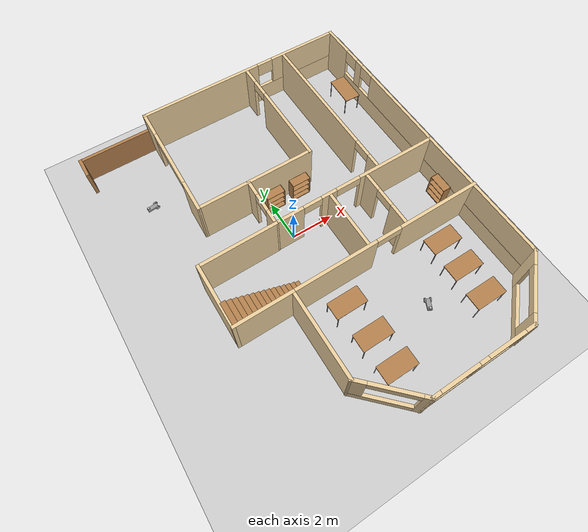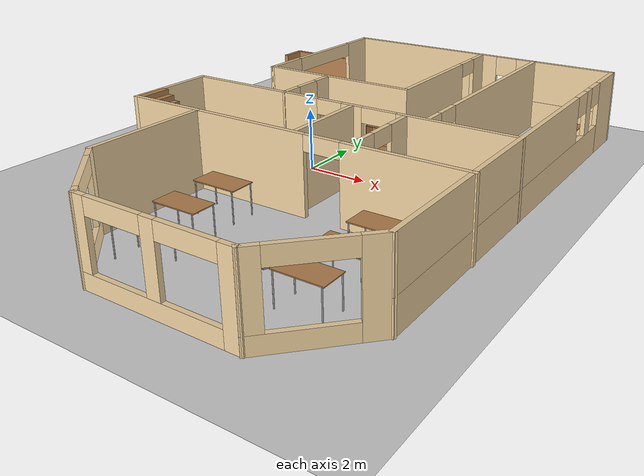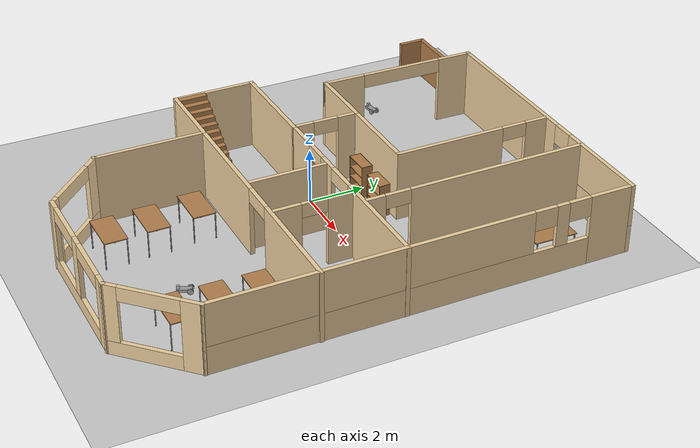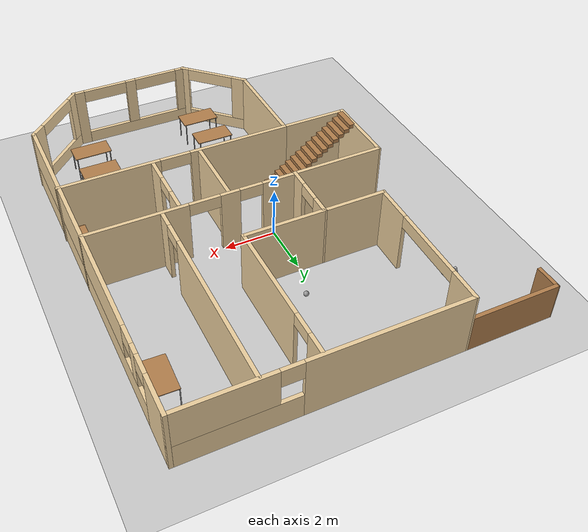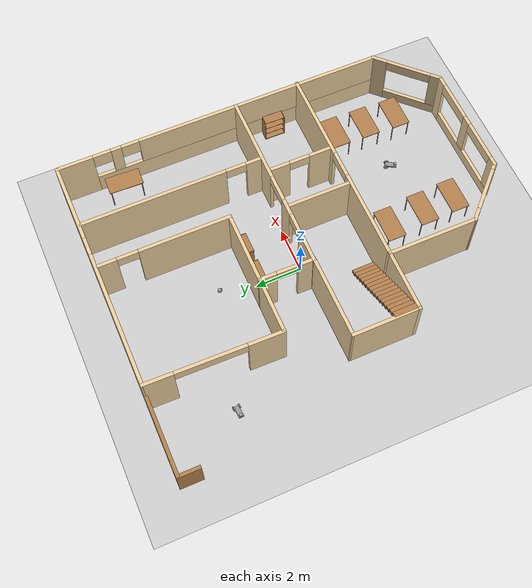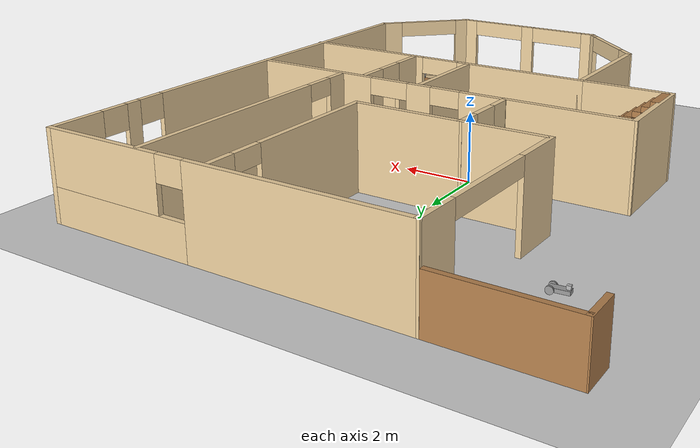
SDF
<sdf version="1.6">
 <world name="default">
  <plugin name="welcome" filename="libwelcome.so"/>
  <light name="sun" type="directional">
   <pose>0 0 10 0 -0 0</pose>
   <diffuse>0.8 0.8 0.8 1</diffuse>
   <specular>0.2 0.2 0.2 1</specular>
   <attenuation>
    <range>1000</range>
    <constant>0.9</constant>
    <linear>0.01</linear>
    <quadratic>0.001</quadratic>
   </attenuation>
   <direction>-0.5 0.1 -0.9</direction>
  </light>
  <model name="ground_plane">
   <static>1</static>
   <link name="link">
    <collision name="collision">
     <geometry><plane><normal>0 0 1</normal><size>100 100</size></plane></geometry>
     <surface>
      <contact><collide_bitmask>65535</collide_bitmask></contact>
      <friction><ode><mu>100</mu><mu2>50</mu2></ode></friction>
     </surface>
    </collision>
    <visual name="visual">
     <cast_shadows>0</cast_shadows>
     <geometry><plane><normal>0 0 1</normal><size>100 100</size></plane></geometry>
     <material>
      <script><uri>file://media/materials/scripts/gazebo.material</uri><name>Gazebo/Grey</name></script>
     </material>
    </visual>
   </link>
  </model>
  <gravity>0 0 -9.8</gravity>
  <magnetic_field>6e-06 2.3e-05 -4.2e-05</magnetic_field>
  <atmosphere type="adiabatic"/>
  <physics name="default_physics" default="0" type="ode">
   <max_step_size>0.001</max_step_size>
   <real_time_factor>1</real_time_factor>
   <real_time_update_rate>1000</real_time_update_rate>
  </physics>
  <scene><ambient>0.4 0.4 0.4 1</ambient><background>0.7 0.7 0.7 1</background><shadows>1</shadows></scene>
  <spherical_coordinates>
   <surface_model>EARTH_WGS84</surface_model>
   <latitude_deg>0</latitude_deg>
   <longitude_deg>0</longitude_deg>
   <elevation>0</elevation>
   <heading_deg>0</heading_deg>
  </spherical_coordinates>
  <model name="Building">
   <pose>0.288686 -0.504373 0 0 -0 0</pose>
   <link name="Stairs_2">
    <visual name="Stairs_2_Visual_0">
     <pose>-1.38684 -1.94916 0.083333 0 -0 -1.5708</pose>
     <geometry><box><size>1 0.233333 0.166667</size></box></geometry>
     <material>
      <script><uri>file://media/materials/scripts/gazebo.material</uri><name>Gazebo/Wood</name></script>
      <ambient>0.760784 0.662745 0.627451 1</ambient>
     </material>
     <meta><layer>0</layer></meta>
    </visual>
    <collision name="Stairs_2_Collision_0">
     <geometry><box><size>1 0.233333 0.166667</size></box></geometry>
     <pose>-1.38684 -1.94916 0.083333 0 -0 -1.5708</pose>
    </collision>
    <visual name="Stairs_2_Visual_1">
     <pose>-1.62017 -1.94916 0.25 0 -0 -1.5708</pose>
     <geometry><box><size>1 0.233333 0.166667</size></box></geometry>
     <material>
      <script><uri>file://media/materials/scripts/gazebo.material</uri><name>Gazebo/Wood</name></script>
      <ambient>0.760784 0.662745 0.627451 1</ambient>
     </material>
     <meta><layer>0</layer></meta>
    </visual>
    <collision name="Stairs_2_Collision_1">
     <geometry><box><size>1 0.233333 0.166667</size></box></geometry>
     <pose>-1.62017 -1.94916 0.25 0 -0 -1.5708</pose>
    </collision>
    <visual name="Stairs_2_Visual_2">
     <pose>-1.85351 -1.94916 0.416667 0 -0 -1.5708</pose>
     <geometry><box><size>1 0.233333 0.166667</size></box></geometry>
     <material>
      <script><uri>file://media/materials/scripts/gazebo.material</uri><name>Gazebo/Wood</name></script>
      <ambient>0.760784 0.662745 0.627451 1</ambient>
     </material>
     <meta><layer>0</layer></meta>
    </visual>
    <collision name="Stairs_2_Collision_2">
     <geometry><box><size>1 0.233333 0.166667</size></box></geometry>
     <pose>-1.85351 -1.94916 0.416667 0 -0 -1.5708</pose>
    </collision>
    <visual name="Stairs_2_Visual_3">
     <pose>-2.08684 -1.94916 0.583333 0 -0 -1.5708</pose>
     <geometry><box><size>1 0.233333 0.166667</size></box></geometry>
     <material>
      <script><uri>file://media/materials/scripts/gazebo.material</uri><name>Gazebo/Wood</name></script>
      <ambient>0.760784 0.662745 0.627451 1</ambient>
     </material>
     <meta><layer>0</layer></meta>
    </visual>
    <collision name="Stairs_2_Collision_3">
     <geometry><box><size>1 0.233333 0.166667</size></box></geometry>
     <pose>-2.08684 -1.94916 0.583333 0 -0 -1.5708</pose>
    </collision>
    <visual name="Stairs_2_Visual_4">
     <pose>-2.32017 -1.94916 0.75 0 -0 -1.5708</pose>
     <geometry><box><size>1 0.233333 0.166667</size></box></geometry>
     <material>
      <script><uri>file://media/materials/scripts/gazebo.material</uri><name>Gazebo/Wood</name></script>
      <ambient>0.760784 0.662745 0.627451 1</ambient>
     </material>
     <meta><layer>0</layer></meta>
    </visual>
    <collision name="Stairs_2_Collision_4">
     <geometry><box><size>1 0.233333 0.166667</size></box></geometry>
     <pose>-2.32017 -1.94916 0.75 0 -0 -1.5708</pose>
    </collision>
    <visual name="Stairs_2_Visual_5">
     <pose>-2.55351 -1.94916 0.916667 0 -0 -1.5708</pose>
     <geometry><box><size>1 0.233333 0.166667</size></box></geometry>
     <material>
      <script><uri>file://media/materials/scripts/gazebo.material</uri><name>Gazebo/Wood</name></script>
      <ambient>0.760784 0.662745 0.627451 1</ambient>
     </material>
     <meta><layer>0</layer></meta>
    </visual>
    <collision name="Stairs_2_Collision_5">
     <geometry><box><size>1 0.233333 0.166667</size></box></geometry>
     <pose>-2.55351 -1.94916 0.916667 0 -0 -1.5708</pose>
    </collision>
    <visual name="Stairs_2_Visual_6">
     <pose>-2.78684 -1.94916 1.08333 0 -0 -1.5708</pose>
     <geometry><box><size>1 0.233333 0.166667</size></box></geometry>
     <material>
      <script><uri>file://media/materials/scripts/gazebo.material</uri><name>Gazebo/Wood</name></script>
      <ambient>0.760784 0.662745 0.627451 1</ambient>
     </material>
     <meta><layer>0</layer></meta>
    </visual>
    <collision name="Stairs_2_Collision_6">
     <geometry><box><size>1 0.233333 0.166667</size></box></geometry>
     <pose>-2.78684 -1.94916 1.08333 0 -0 -1.5708</pose>
    </collision>
    <visual name="Stairs_2_Visual_7">
     <pose>-3.02017 -1.94916 1.25 0 -0 -1.5708</pose>
     <geometry><box><size>1 0.233333 0.166667</size></box></geometry>
     <material>
      <script><uri>file://media/materials/scripts/gazebo.material</uri><name>Gazebo/Wood</name></script>
      <ambient>0.760784 0.662745 0.627451 1</ambient>
     </material>
     <meta><layer>0</layer></meta>
    </visual>
    <collision name="Stairs_2_Collision_7">
     <geometry><box><size>1 0.233333 0.166667</size></box></geometry>
     <pose>-3.02017 -1.94916 1.25 0 -0 -1.5708</pose>
    </collision>
    <visual name="Stairs_2_Visual_8">
     <pose>-3.25351 -1.94916 1.41667 0 -0 -1.5708</pose>
     <geometry><box><size>1 0.233333 0.166667</size></box></geometry>
     <material>
      <script><uri>file://media/materials/scripts/gazebo.material</uri><name>Gazebo/Wood</name></script>
      <ambient>0.760784 0.662745 0.627451 1</ambient>
     </material>
     <meta><layer>0</layer></meta>
    </visual>
    <collision name="Stairs_2_Collision_8">
     <geometry><box><size>1 0.233333 0.166667</size></box></geometry>
     <pose>-3.25351 -1.94916 1.41667 0 -0 -1.5708</pose>
    </collision>
    <visual name="Stairs_2_Visual_9">
     <pose>-3.48684 -1.94916 1.58333 0 -0 -1.5708</pose>
     <geometry><box><size>1 0.233333 0.166667</size></box></geometry>
     <material>
      <script><uri>file://media/materials/scripts/gazebo.material</uri><name>Gazebo/Wood</name></script>
      <ambient>0.760784 0.662745 0.627451 1</ambient>
     </material>
     <meta><layer>0</layer></meta>
    </visual>
    <collision name="Stairs_2_Collision_9">
     <geometry><box><size>1 0.233333 0.166667</size></box></geometry>
     <pose>-3.48684 -1.94916 1.58333 0 -0 -1.5708</pose>
    </collision>
    <visual name="Stairs_2_Visual_10">
     <pose>-3.72017 -1.94916 1.75 0 -0 -1.5708</pose>
     <geometry><box><size>1 0.233333 0.166667</size></box></geometry>
     <material>
      <script><uri>file://media/materials/scripts/gazebo.material</uri><name>Gazebo/Wood</name></script>
      <ambient>0.760784 0.662745 0.627451 1</ambient>
     </material>
     <meta><layer>0</layer></meta>
    </visual>
    <collision name="Stairs_2_Collision_10">
     <geometry><box><size>1 0.233333 0.166667</size></box></geometry>
     <pose>-3.72017 -1.94916 1.75 0 -0 -1.5708</pose>
    </collision>
    <visual name="Stairs_2_Visual_11">
     <pose>-3.95351 -1.94916 1.91667 0 -0 -1.5708</pose>
     <geometry><box><size>1 0.233333 0.166667</size></box></geometry>
     <material>
      <script><uri>file://media/materials/scripts/gazebo.material</uri><name>Gazebo/Wood</name></script>
      <ambient>0.760784 0.662745 0.627451 1</ambient>
     </material>
     <meta><layer>0</layer></meta>
    </visual>
    <collision name="Stairs_2_Collision_11">
     <geometry><box><size>1 0.233333 0.166667</size></box></geometry>
     <pose>-3.95351 -1.94916 1.91667 0 -0 -1.5708</pose>
    </collision>
    <visual name="Stairs_2_Visual_12">
     <pose>-4.18684 -1.94916 2.08333 0 -0 -1.5708</pose>
     <geometry><box><size>1 0.233333 0.166667</size></box></geometry>
     <material>
      <script><uri>file://media/materials/scripts/gazebo.material</uri><name>Gazebo/Wood</name></script>
      <ambient>0.760784 0.662745 0.627451 1</ambient>
     </material>
     <meta><layer>0</layer></meta>
    </visual>
    <collision name="Stairs_2_Collision_12">
     <geometry><box><size>1 0.233333 0.166667</size></box></geometry>
     <pose>-4.18684 -1.94916 2.08333 0 -0 -1.5708</pose>
    </collision>
    <visual name="Stairs_2_Visual_13">
     <pose>-4.42017 -1.94916 2.25 0 -0 -1.5708</pose>
     <geometry><box><size>1 0.233333 0.166667</size></box></geometry>
     <material>
      <script><uri>file://media/materials/scripts/gazebo.material</uri><name>Gazebo/Wood</name></script>
      <ambient>0.760784 0.662745 0.627451 1</ambient>
     </material>
     <meta><layer>0</layer></meta>
    </visual>
    <collision name="Stairs_2_Collision_13">
     <geometry><box><size>1 0.233333 0.166667</size></box></geometry>
     <pose>-4.42017 -1.94916 2.25 0 -0 -1.5708</pose>
    </collision>
    <visual name="Stairs_2_Visual_14">
     <pose>-4.65351 -1.94916 2.41667 0 -0 -1.5708</pose>
     <geometry><box><size>1 0.233333 0.166667</size></box></geometry>
     <material>
      <script><uri>file://media/materials/scripts/gazebo.material</uri><name>Gazebo/Wood</name></script>
      <ambient>0.760784 0.662745 0.627451 1</ambient>
     </material>
     <meta><layer>0</layer></meta>
    </visual>
    <collision name="Stairs_2_Collision_14">
     <geometry><box><size>1 0.233333 0.166667</size></box></geometry>
     <pose>-4.65351 -1.94916 2.41667 0 -0 -1.5708</pose>
    </collision>
   </link>
   <link name="Wall_34">
    <pose>6.87523 1.11069 0 0 0 -1.5708</pose>
    <visual name="Wall_34_Visual_0">
     <pose>-6.55765 0 1.25 0 -0 0</pose>
     <geometry><box><size>1.6347 0.15 2.5</size></box></geometry>
     <material>
      <script><uri>file://media/materials/scripts/gazebo.material</uri><name>Gazebo/Grey</name></script>
      <ambient>0.921569 0.807843 0.615686 1</ambient>
     </material>
     <meta><layer>0</layer></meta>
    </visual>
    <collision name="Wall_34_Collision_0">
     <geometry><box><size>1.6347 0.15 2.5</size></box></geometry>
     <pose>-6.55765 0 1.25 0 -0 0</pose>
    </collision>
    <visual name="Wall_34_Visual_1">
     <pose>0.81735 0 0.5 0 -0 0</pose>
     <geometry><box><size>13.1153 0.15 1</size></box></geometry>
     <material>
      <script><uri>file://media/materials/scripts/gazebo.material</uri><name>Gazebo/Grey</name></script>
      <ambient>0.921569 0.807843 0.615686 1</ambient>
     </material>
     <meta><layer>0</layer></meta>
    </visual>
    <collision name="Wall_34_Collision_1">
     <geometry><box><size>13.1153 0.15 1</size></box></geometry>
     <pose>0.81735 0 0.5 0 -0 0</pose>
    </collision>
    <visual name="Wall_34_Visual_2">
     <pose>-4.71674 0 1.75 0 -0 0</pose>
     <geometry><box><size>0.447118 0.15 1.5</size></box></geometry>
     <material>
      <script><uri>file://media/materials/scripts/gazebo.material</uri><name>Gazebo/Grey</name></script>
      <ambient>0.921569 0.807843 0.615686 1</ambient>
     </material>
     <meta><layer>0</layer></meta>
    </visual>
    <collision name="Wall_34_Collision_2">
     <geometry><box><size>0.447118 0.15 1.5</size></box></geometry>
     <pose>-4.71674 0 1.75 0 -0 0</pose>
    </collision>
    <visual name="Wall_34_Visual_3">
     <pose>1.84091 0 1.75 0 -0 0</pose>
     <geometry><box><size>11.0682 0.15 1.5</size></box></geometry>
     <material>
      <script><uri>file://media/materials/scripts/gazebo.material</uri><name>Gazebo/Grey</name></script>
      <ambient>0.921569 0.807843 0.615686 1</ambient>
     </material>
     <meta><layer>0</layer></meta>
    </visual>
    <collision name="Wall_34_Collision_3">
     <geometry><box><size>11.0682 0.15 1.5</size></box></geometry>
     <pose>1.84091 0 1.75 0 -0 0</pose>
    </collision>
    <visual name="Wall_34_Visual_4">
     <pose>-5.3403 0 2.15 0 -0 0</pose>
     <geometry><box><size>0.8 0.15 0.7</size></box></geometry>
     <material>
      <script><uri>file://media/materials/scripts/gazebo.material</uri><name>Gazebo/Grey</name></script>
      <ambient>0.921569 0.807843 0.615686 1</ambient>
     </material>
     <meta><layer>0</layer></meta>
    </visual>
    <collision name="Wall_34_Collision_4">
     <geometry><box><size>0.8 0.15 0.7</size></box></geometry>
     <pose>-5.3403 0 2.15 0 -0 0</pose>
    </collision>
    <visual name="Wall_34_Visual_5">
     <pose>-4.09318 0 2.15 0 -0 0</pose>
     <geometry><box><size>0.8 0.15 0.7</size></box></geometry>
     <material>
      <script><uri>file://media/materials/scripts/gazebo.material</uri><name>Gazebo/Grey</name></script>
      <ambient>0.921569 0.807843 0.615686 1</ambient>
     </material>
     <meta><layer>0</layer></meta>
    </visual>
    <collision name="Wall_34_Collision_5">
     <geometry><box><size>0.8 0.15 0.7</size></box></geometry>
     <pose>-4.09318 0 2.15 0 -0 0</pose>
    </collision>
   </link>
   <link name="Wall_35">
    <pose>5.77921 -7.28533 0 0 0 -2.35619</pose>
    <visual name="Wall_35_Visual_0">
     <pose>-1.26324 0 1.25 0 -0 0</pose>
     <geometry><box><size>0.723512 0.15 2.5</size></box></geometry>
     <material>
      <script><uri>file://media/materials/scripts/gazebo.material</uri><name>Gazebo/Grey</name></script>
      <ambient>0.921569 0.807843 0.615686 1</ambient>
     </material>
     <meta><layer>0</layer></meta>
    </visual>
    <collision name="Wall_35_Collision_0">
     <geometry><box><size>0.723512 0.15 2.5</size></box></geometry>
     <pose>-1.26324 0 1.25 0 -0 0</pose>
    </collision>
    <visual name="Wall_35_Visual_1">
     <pose>0.361756 0 0.25 0 -0 0</pose>
     <geometry><box><size>2.52649 0.15 0.5</size></box></geometry>
     <material>
      <script><uri>file://media/materials/scripts/gazebo.material</uri><name>Gazebo/Grey</name></script>
      <ambient>0.921569 0.807843 0.615686 1</ambient>
     </material>
     <meta><layer>0</layer></meta>
    </visual>
    <collision name="Wall_35_Collision_1">
     <geometry><box><size>2.52649 0.15 0.5</size></box></geometry>
     <pose>0.361756 0 0.25 0 -0 0</pose>
    </collision>
    <visual name="Wall_35_Visual_2">
     <pose>1.36176 0 1.5 0 -0 0</pose>
     <geometry><box><size>0.526488 0.15 2</size></box></geometry>
     <material>
      <script><uri>file://media/materials/scripts/gazebo.material</uri><name>Gazebo/Grey</name></script>
      <ambient>0.921569 0.807843 0.615686 1</ambient>
     </material>
     <meta><layer>0</layer></meta>
    </visual>
    <collision name="Wall_35_Collision_2">
     <geometry><box><size>0.526488 0.15 2</size></box></geometry>
     <pose>1.36176 0 1.5 0 -0 0</pose>
    </collision>
    <visual name="Wall_35_Visual_3">
     <pose>0.098512 0 2.25 0 -0 0</pose>
     <geometry><box><size>2 0.15 0.5</size></box></geometry>
     <material>
      <script><uri>file://media/materials/scripts/gazebo.material</uri><name>Gazebo/Grey</name></script>
      <ambient>0.921569 0.807843 0.615686 1</ambient>
     </material>
     <meta><layer>0</layer></meta>
    </visual>
    <collision name="Wall_35_Collision_3">
     <geometry><box><size>2 0.15 0.5</size></box></geometry>
     <pose>0.098512 0 2.25 0 -0 0</pose>
    </collision>
   </link>
   <link name="Wall_36">
    <pose>2.2582 -8.38134 0 0 -0 3.14159</pose>
    <visual name="Wall_36_Visual_0">
     <pose>-2.23916 0 1.25 0 -0 0</pose>
     <geometry><box><size>0.521674 0.15 2.5</size></box></geometry>
     <material>
      <script><uri>file://media/materials/scripts/gazebo.material</uri><name>Gazebo/Grey</name></script>
      <ambient>0.921569 0.807843 0.615686 1</ambient>
     </material>
     <meta><layer>0</layer></meta>
    </visual>
    <collision name="Wall_36_Collision_0">
     <geometry><box><size>0.521674 0.15 2.5</size></box></geometry>
     <pose>-2.23916 0 1.25 0 -0 0</pose>
    </collision>
    <visual name="Wall_36_Visual_1">
     <pose>0.260837 0 0.25 0 -0 0</pose>
     <geometry><box><size>4.47833 0.15 0.5</size></box></geometry>
     <material>
      <script><uri>file://media/materials/scripts/gazebo.material</uri><name>Gazebo/Grey</name></script>
      <ambient>0.921569 0.807843 0.615686 1</ambient>
     </material>
     <meta><layer>0</layer></meta>
    </visual>
    <collision name="Wall_36_Collision_1">
     <geometry><box><size>4.47833 0.15 0.5</size></box></geometry>
     <pose>0.260837 0 0.25 0 -0 0</pose>
    </collision>
    <visual name="Wall_36_Visual_2">
     <pose>0.035742 0 1.5 0 -0 0</pose>
     <geometry><box><size>0.428135 0.15 2</size></box></geometry>
     <material>
      <script><uri>file://media/materials/scripts/gazebo.material</uri><name>Gazebo/Grey</name></script>
      <ambient>0.921569 0.807843 0.615686 1</ambient>
     </material>
     <meta><layer>0</layer></meta>
    </visual>
    <collision name="Wall_36_Collision_2">
     <geometry><box><size>0.428135 0.15 2</size></box></geometry>
     <pose>0.035742 0 1.5 0 -0 0</pose>
    </collision>
    <visual name="Wall_36_Visual_3">
     <pose>2.2749 0 1.5 0 -0 0</pose>
     <geometry><box><size>0.450191 0.15 2</size></box></geometry>
     <material>
      <script><uri>file://media/materials/scripts/gazebo.material</uri><name>Gazebo/Grey</name></script>
      <ambient>0.921569 0.807843 0.615686 1</ambient>
     </material>
     <meta><layer>0</layer></meta>
    </visual>
    <collision name="Wall_36_Collision_3">
     <geometry><box><size>0.450191 0.15 2</size></box></geometry>
     <pose>2.2749 0 1.5 0 -0 0</pose>
    </collision>
    <visual name="Wall_36_Visual_4">
     <pose>-1.07833 0 2.25 0 -0 0</pose>
     <geometry><box><size>1.8 0.15 0.5</size></box></geometry>
     <material>
      <script><uri>file://media/materials/scripts/gazebo.material</uri><name>Gazebo/Grey</name></script>
      <ambient>0.921569 0.807843 0.615686 1</ambient>
     </material>
     <meta><layer>0</layer></meta>
    </visual>
    <collision name="Wall_36_Collision_4">
     <geometry><box><size>1.8 0.15 0.5</size></box></geometry>
     <pose>-1.07833 0 2.25 0 -0 0</pose>
    </collision>
    <visual name="Wall_36_Visual_5">
     <pose>1.14981 0 2.25 0 -0 0</pose>
     <geometry><box><size>1.8 0.15 0.5</size></box></geometry>
     <material>
      <script><uri>file://media/materials/scripts/gazebo.material</uri><name>Gazebo/Grey</name></script>
      <ambient>0.921569 0.807843 0.615686 1</ambient>
     </material>
     <meta><layer>0</layer></meta>
    </visual>
    <collision name="Wall_36_Collision_5">
     <geometry><box><size>1.8 0.15 0.5</size></box></geometry>
     <pose>1.14981 0 2.25 0 -0 0</pose>
    </collision>
   </link>
   <link name="Wall_37">
    <pose>-1.17443 -7.37372 0 0 -0 2.35619</pose>
    <visual name="Wall_37_Visual_0">
     <pose>-1.31904 0 1.25 0 -0 0</pose>
     <geometry><box><size>0.361912 0.15 2.5</size></box></geometry>
     <material>
      <script><uri>file://media/materials/scripts/gazebo.material</uri><name>Gazebo/Grey</name></script>
      <ambient>0.921569 0.807843 0.615686 1</ambient>
     </material>
     <meta><layer>0</layer></meta>
    </visual>
    <collision name="Wall_37_Collision_0">
     <geometry><box><size>0.361912 0.15 2.5</size></box></geometry>
     <pose>-1.31904 0 1.25 0 -0 0</pose>
    </collision>
    <visual name="Wall_37_Visual_1">
     <pose>0.180956 0 0.25 0 -0 0</pose>
     <geometry><box><size>2.63809 0.15 0.5</size></box></geometry>
     <material>
      <script><uri>file://media/materials/scripts/gazebo.material</uri><name>Gazebo/Grey</name></script>
      <ambient>0.921569 0.807843 0.615686 1</ambient>
     </material>
     <meta><layer>0</layer></meta>
    </visual>
    <collision name="Wall_37_Collision_1">
     <geometry><box><size>2.63809 0.15 0.5</size></box></geometry>
     <pose>0.180956 0 0.25 0 -0 0</pose>
    </collision>
    <visual name="Wall_37_Visual_2">
     <pose>1.18096 0 1.5 0 -0 0</pose>
     <geometry><box><size>0.638088 0.15 2</size></box></geometry>
     <material>
      <script><uri>file://media/materials/scripts/gazebo.material</uri><name>Gazebo/Grey</name></script>
      <ambient>0.921569 0.807843 0.615686 1</ambient>
     </material>
     <meta><layer>0</layer></meta>
    </visual>
    <collision name="Wall_37_Collision_2">
     <geometry><box><size>0.638088 0.15 2</size></box></geometry>
     <pose>1.18096 0 1.5 0 -0 0</pose>
    </collision>
    <visual name="Wall_37_Visual_3">
     <pose>-0.138088 0 2.25 0 -0 0</pose>
     <geometry><box><size>2 0.15 0.5</size></box></geometry>
     <material>
      <script><uri>file://media/materials/scripts/gazebo.material</uri><name>Gazebo/Grey</name></script>
      <ambient>0.921569 0.807843 0.615686 1</ambient>
     </material>
     <meta><layer>0</layer></meta>
    </visual>
    <collision name="Wall_37_Collision_3">
     <geometry><box><size>2 0.15 0.5</size></box></geometry>
     <pose>-0.138088 0 2.25 0 -0 0</pose>
    </collision>
   </link>
   <link name="Wall_38">
    <collision name="Wall_38_Collision">
     <geometry><box><size>4 0.15 2.5</size></box></geometry>
     <pose>0 0 1.25 0 -0 0</pose>
    </collision>
    <visual name="Wall_38_Visual">
     <pose>0 0 1.25 0 -0 0</pose>
     <geometry><box><size>4 0.15 2.5</size></box></geometry>
     <material>
      <script><uri>file://media/materials/scripts/gazebo.material</uri><name>Gazebo/Grey</name></script>
      <ambient>0.921569 0.807843 0.615686 1</ambient>
     </material>
     <meta><layer>0</layer></meta>
    </visual>
    <pose>-2.18206 -4.44109 0 0 -0 1.5708</pose>
   </link>
   <link name="Wall_39">
    <collision name="Wall_39_Collision">
     <geometry><box><size>2.75 0.15 2.5</size></box></geometry>
     <pose>0 0 1.25 0 -0 0</pose>
    </collision>
    <visual name="Wall_39_Visual">
     <pose>0 0 1.25 0 -0 0</pose>
     <geometry><box><size>2.75 0.15 2.5</size></box></geometry>
     <material>
      <script><uri>file://media/materials/scripts/gazebo.material</uri><name>Gazebo/Grey</name></script>
      <ambient>0.921569 0.807843 0.615686 1</ambient>
     </material>
     <meta><layer>0</layer></meta>
    </visual>
    <pose>-3.48206 -2.51609 0 0 -0 3.14159</pose>
   </link>
   <link name="Wall_40">
    <collision name="Wall_40_Collision">
     <geometry><box><size>3 0.15 2.5</size></box></geometry>
     <pose>0 0 1.25 0 -0 0</pose>
    </collision>
    <visual name="Wall_40_Visual">
     <pose>0 0 1.25 0 -0 0</pose>
     <geometry><box><size>3 0.15 2.5</size></box></geometry>
     <material>
      <script><uri>file://media/materials/scripts/gazebo.material</uri><name>Gazebo/Grey</name></script>
      <ambient>0.921569 0.807843 0.615686 1</ambient>
     </material>
     <meta><layer>0</layer></meta>
    </visual>
    <pose>-4.78206 -1.09109 0 0 -0 1.5708</pose>
   </link>
   <link name="Wall_41">
    <collision name="Wall_41_Collision">
     <geometry><box><size>3.71526 0.15 2.5</size></box></geometry>
     <pose>0 0 1.25 0 -0 0</pose>
    </collision>
    <visual name="Wall_41_Visual">
     <pose>0 0 1.25 0 -0 0</pose>
     <geometry><box><size>3.71526 0.15 2.5</size></box></geometry>
     <material>
      <script><uri>file://media/materials/scripts/gazebo.material</uri><name>Gazebo/Grey</name></script>
      <ambient>0.921569 0.807843 0.615686 1</ambient>
     </material>
     <meta><layer>0</layer></meta>
    </visual>
    <pose>-2.99945 0.342607 0 0 -0 0.004878</pose>
   </link>
   <link name="Wall_42">
    <pose>-1.19945 1.51761 0 0 -0 1.55589</pose>
    <visual name="Wall_42_Visual_0">
     <pose>-0.846422 0 1.25 0 -0 0</pose>
     <geometry><box><size>0.790024 0.15 2.5</size></box></geometry>
     <material>
      <script><uri>file://media/materials/scripts/gazebo.material</uri><name>Gazebo/Grey</name></script>
      <ambient>0.921569 0.807843 0.615686 1</ambient>
     </material>
     <meta><layer>0</layer></meta>
    </visual>
    <collision name="Wall_42_Collision_0">
     <geometry><box><size>0.790024 0.15 2.5</size></box></geometry>
     <pose>-0.846422 0 1.25 0 -0 0</pose>
    </collision>
    <visual name="Wall_42_Visual_1">
     <pose>0.845012 0 1.25 0 -0 0</pose>
     <geometry><box><size>0.792844 0.15 2.5</size></box></geometry>
     <material>
      <script><uri>file://media/materials/scripts/gazebo.material</uri><name>Gazebo/Grey</name></script>
      <ambient>0.921569 0.807843 0.615686 1</ambient>
     </material>
     <meta><layer>0</layer></meta>
    </visual>
    <collision name="Wall_42_Collision_1">
     <geometry><box><size>0.792844 0.15 2.5</size></box></geometry>
     <pose>0.845012 0 1.25 0 -0 0</pose>
    </collision>
    <visual name="Wall_42_Visual_2">
     <pose>-0.00141 0 2.25 0 -0 0</pose>
     <geometry><box><size>0.9 0.15 0.5</size></box></geometry>
     <material>
      <script><uri>file://media/materials/scripts/gazebo.material</uri><name>Gazebo/Grey</name></script>
      <ambient>0.921569 0.807843 0.615686 1</ambient>
     </material>
     <meta><layer>0</layer></meta>
    </visual>
    <collision name="Wall_42_Collision_2">
     <geometry><box><size>0.9 0.15 0.5</size></box></geometry>
     <pose>-0.00141 0 2.25 0 -0 0</pose>
    </collision>
   </link>
   <link name="Wall_43">
    <collision name="Wall_43_Collision">
     <geometry><box><size>2.48416 0.15 2.5</size></box></geometry>
     <pose>0 0 1.25 0 -0 0</pose>
    </collision>
    <visual name="Wall_43_Visual">
     <pose>0 0 1.25 0 -0 0</pose>
     <geometry><box><size>2.48416 0.15 2.5</size></box></geometry>
     <material>
      <script><uri>file://media/materials/scripts/gazebo.material</uri><name>Gazebo/Grey</name></script>
      <ambient>0.921569 0.807843 0.615686 1</ambient>
     </material>
     <meta><layer>0</layer></meta>
    </visual>
    <pose>-2.34914 2.68391 0 0 -0 3.14159</pose>
   </link>
   <link name="Wall_44">
    <pose>-3.51813 5.54739 0 0 -0 1.5501</pose>
    <visual name="Wall_44_Visual_0">
     <pose>-2.15687 0 1.25 0 -0 0</pose>
     <geometry><box><size>1.56445 0.15 2.5</size></box></geometry>
     <material>
      <script><uri>file://media/materials/scripts/gazebo.material</uri><name>Gazebo/Grey</name></script>
      <ambient>0.921569 0.807843 0.615686 1</ambient>
     </material>
     <meta><layer>0</layer></meta>
    </visual>
    <collision name="Wall_44_Collision_0">
     <geometry><box><size>1.56445 0.15 2.5</size></box></geometry>
     <pose>-2.15687 0 1.25 0 -0 0</pose>
    </collision>
    <visual name="Wall_44_Visual_1">
     <pose>2.28222 0 1.25 0 -0 0</pose>
     <geometry><box><size>1.31374 0.15 2.5</size></box></geometry>
     <material>
      <script><uri>file://media/materials/scripts/gazebo.material</uri><name>Gazebo/Grey</name></script>
      <ambient>0.921569 0.807843 0.615686 1</ambient>
     </material>
     <meta><layer>0</layer></meta>
    </visual>
    <collision name="Wall_44_Collision_1">
     <geometry><box><size>1.31374 0.15 2.5</size></box></geometry>
     <pose>2.28222 0 1.25 0 -0 0</pose>
    </collision>
    <visual name="Wall_44_Visual_2">
     <pose>0.125356 0 2.25 0 -0 0</pose>
     <geometry><box><size>3 0.15 0.5</size></box></geometry>
     <material>
      <script><uri>file://media/materials/scripts/gazebo.material</uri><name>Gazebo/Grey</name></script>
      <ambient>0.921569 0.807843 0.615686 1</ambient>
     </material>
     <meta><layer>0</layer></meta>
    </visual>
    <collision name="Wall_44_Collision_2">
     <geometry><box><size>3 0.15 0.5</size></box></geometry>
     <pose>0.125356 0 2.25 0 -0 0</pose>
    </collision>
   </link>
   <link name="Wall_45">
    <pose>1.70819 8.41078 0 0 0 -1.8e-05</pose>
    <visual name="Wall_45_Visual_0">
     <pose>-2.20454 0 1.25 0 -0 0</pose>
     <geometry><box><size>6.07508 0.15 2.5</size></box></geometry>
     <material>
      <script><uri>file://media/materials/scripts/gazebo.material</uri><name>Gazebo/Grey</name></script>
      <ambient>0.921569 0.807843 0.615686 1</ambient>
     </material>
     <meta><layer>0</layer></meta>
    </visual>
    <collision name="Wall_45_Collision_0">
     <geometry><box><size>6.07508 0.15 2.5</size></box></geometry>
     <pose>-2.20454 0 1.25 0 -0 0</pose>
    </collision>
    <visual name="Wall_45_Visual_1">
     <pose>3.03754 0 0.5 0 -0 0</pose>
     <geometry><box><size>4.40909 0.15 1</size></box></geometry>
     <material>
      <script><uri>file://media/materials/scripts/gazebo.material</uri><name>Gazebo/Grey</name></script>
      <ambient>0.921569 0.807843 0.615686 1</ambient>
     </material>
     <meta><layer>0</layer></meta>
    </visual>
    <collision name="Wall_45_Collision_1">
     <geometry><box><size>4.40909 0.15 1</size></box></geometry>
     <pose>3.03754 0 0.5 0 -0 0</pose>
    </collision>
    <visual name="Wall_45_Visual_2">
     <pose>3.43754 0 1.75 0 -0 0</pose>
     <geometry><box><size>3.60909 0.15 1.5</size></box></geometry>
     <material>
      <script><uri>file://media/materials/scripts/gazebo.material</uri><name>Gazebo/Grey</name></script>
      <ambient>0.921569 0.807843 0.615686 1</ambient>
     </material>
     <meta><layer>0</layer></meta>
    </visual>
    <collision name="Wall_45_Collision_2">
     <geometry><box><size>3.60909 0.15 1.5</size></box></geometry>
     <pose>3.43754 0 1.75 0 -0 0</pose>
    </collision>
    <visual name="Wall_45_Visual_3">
     <pose>1.233 0 2.15 0 -0 0</pose>
     <geometry><box><size>0.8 0.15 0.7</size></box></geometry>
     <material>
      <script><uri>file://media/materials/scripts/gazebo.material</uri><name>Gazebo/Grey</name></script>
      <ambient>0.921569 0.807843 0.615686 1</ambient>
     </material>
     <meta><layer>0</layer></meta>
    </visual>
    <collision name="Wall_45_Collision_3">
     <geometry><box><size>0.8 0.15 0.7</size></box></geometry>
     <pose>1.233 0 2.15 0 -0 0</pose>
    </collision>
   </link>
   <link name="Wall_47">
    <pose>2.36794 -2.51609 0 0 -0 0</pose>
    <visual name="Wall_47_Visual_0">
     <pose>-2.59572 0 1.25 0 -0 0</pose>
     <geometry><box><size>4.05855 0.15 2.5</size></box></geometry>
     <material>
      <script><uri>file://media/materials/scripts/gazebo.material</uri><name>Gazebo/Grey</name></script>
      <ambient>0.921569 0.807843 0.615686 1</ambient>
     </material>
     <meta><layer>0</layer></meta>
    </visual>
    <collision name="Wall_47_Collision_0">
     <geometry><box><size>4.05855 0.15 2.5</size></box></geometry>
     <pose>-2.59572 0 1.25 0 -0 0</pose>
    </collision>
    <visual name="Wall_47_Visual_1">
     <pose>2.62928 0 1.25 0 -0 0</pose>
     <geometry><box><size>3.99145 0.15 2.5</size></box></geometry>
     <material>
      <script><uri>file://media/materials/scripts/gazebo.material</uri><name>Gazebo/Grey</name></script>
      <ambient>0.921569 0.807843 0.615686 1</ambient>
     </material>
     <meta><layer>0</layer></meta>
    </visual>
    <collision name="Wall_47_Collision_1">
     <geometry><box><size>3.99145 0.15 2.5</size></box></geometry>
     <pose>2.62928 0 1.25 0 -0 0</pose>
    </collision>
    <visual name="Wall_47_Visual_2">
     <pose>0.033554 0 2.25 0 -0 0</pose>
     <geometry><box><size>1.2 0.15 0.5</size></box></geometry>
     <material>
      <script><uri>file://media/materials/scripts/gazebo.material</uri><name>Gazebo/Grey</name></script>
      <ambient>0.921569 0.807843 0.615686 1</ambient>
     </material>
     <meta><layer>0</layer></meta>
    </visual>
    <collision name="Wall_47_Collision_2">
     <geometry><box><size>1.2 0.15 0.5</size></box></geometry>
     <pose>0.033554 0 2.25 0 -0 0</pose>
    </collision>
   </link>
   <link name="Wall_49">
    <pose>2.83316 0.368694 0 0 -0 0</pose>
    <visual name="Wall_49_Visual_0">
     <pose>-3.41637 0 1.25 0 -0 0</pose>
     <geometry><box><size>1.41725 0.15 2.5</size></box></geometry>
     <material>
      <script><uri>file://media/materials/scripts/gazebo.material</uri><name>Gazebo/Grey</name></script>
      <ambient>0.921569 0.807843 0.615686 1</ambient>
     </material>
     <meta><layer>0</layer></meta>
    </visual>
    <collision name="Wall_49_Collision_0">
     <geometry><box><size>1.41725 0.15 2.5</size></box></geometry>
     <pose>-3.41637 0 1.25 0 -0 0</pose>
    </collision>
    <visual name="Wall_49_Visual_1">
     <pose>-1.4284 0 1.25 0 -0 0</pose>
     <geometry><box><size>0.758696 0.15 2.5</size></box></geometry>
     <material>
      <script><uri>file://media/materials/scripts/gazebo.material</uri><name>Gazebo/Grey</name></script>
      <ambient>0.921569 0.807843 0.615686 1</ambient>
     </material>
     <meta><layer>0</layer></meta>
    </visual>
    <collision name="Wall_49_Collision_1">
     <geometry><box><size>0.758696 0.15 2.5</size></box></geometry>
     <pose>-1.4284 0 1.25 0 -0 0</pose>
    </collision>
    <visual name="Wall_49_Visual_2">
     <pose>2.13797 0 1.25 0 -0 0</pose>
     <geometry><box><size>3.97405 0.15 2.5</size></box></geometry>
     <material>
      <script><uri>file://media/materials/scripts/gazebo.material</uri><name>Gazebo/Grey</name></script>
      <ambient>0.921569 0.807843 0.615686 1</ambient>
     </material>
     <meta><layer>0</layer></meta>
    </visual>
    <collision name="Wall_49_Collision_2">
     <geometry><box><size>3.97405 0.15 2.5</size></box></geometry>
     <pose>2.13797 0 1.25 0 -0 0</pose>
    </collision>
    <visual name="Wall_49_Visual_3">
     <pose>-2.25775 0 2.25 0 -0 0</pose>
     <geometry><box><size>0.9 0.15 0.5</size></box></geometry>
     <material>
      <script><uri>file://media/materials/scripts/gazebo.material</uri><name>Gazebo/Grey</name></script>
      <ambient>0.921569 0.807843 0.615686 1</ambient>
     </material>
     <meta><layer>0</layer></meta>
    </visual>
    <collision name="Wall_49_Collision_3">
     <geometry><box><size>0.9 0.15 0.5</size></box></geometry>
     <pose>-2.25775 0 2.25 0 -0 0</pose>
    </collision>
    <visual name="Wall_49_Visual_4">
     <pose>-0.449054 0 2.25 0 -0 0</pose>
     <geometry><box><size>1.2 0.15 0.5</size></box></geometry>
     <material>
      <script><uri>file://media/materials/scripts/gazebo.material</uri><name>Gazebo/Grey</name></script>
      <ambient>0.921569 0.807843 0.615686 1</ambient>
     </material>
     <meta><layer>0</layer></meta>
    </visual>
    <collision name="Wall_49_Collision_4">
     <geometry><box><size>1.2 0.15 0.5</size></box></geometry>
     <pose>-0.449054 0 2.25 0 -0 0</pose>
    </collision>
   </link>
   <link name="Wall_53">
    <pose>3.31095 -1.0887 0 0 -0 1.5708</pose>
    <visual name="Wall_53_Visual_0">
     <pose>-0.882049 0 1.25 0 -0 0</pose>
     <geometry><box><size>0.985902 0.15 2.5</size></box></geometry>
     <material>
      <script><uri>file://media/materials/scripts/gazebo.material</uri><name>Gazebo/Grey</name></script>
      <ambient>0.921569 0.807843 0.615686 1</ambient>
     </material>
     <meta><layer>0</layer></meta>
    </visual>
    <collision name="Wall_53_Collision_0">
     <geometry><box><size>0.985902 0.15 2.5</size></box></geometry>
     <pose>-0.882049 0 1.25 0 -0 0</pose>
    </collision>
    <visual name="Wall_53_Visual_1">
     <pose>0.942951 0 1.25 0 -0 0</pose>
     <geometry><box><size>0.864098 0.15 2.5</size></box></geometry>
     <material>
      <script><uri>file://media/materials/scripts/gazebo.material</uri><name>Gazebo/Grey</name></script>
      <ambient>0.921569 0.807843 0.615686 1</ambient>
     </material>
     <meta><layer>0</layer></meta>
    </visual>
    <collision name="Wall_53_Collision_1">
     <geometry><box><size>0.864098 0.15 2.5</size></box></geometry>
     <pose>0.942951 0 1.25 0 -0 0</pose>
    </collision>
    <visual name="Wall_53_Visual_2">
     <pose>0.060902 0 2.25 0 -0 0</pose>
     <geometry><box><size>0.9 0.15 0.5</size></box></geometry>
     <material>
      <script><uri>file://media/materials/scripts/gazebo.material</uri><name>Gazebo/Grey</name></script>
      <ambient>0.921569 0.807843 0.615686 1</ambient>
     </material>
     <meta><layer>0</layer></meta>
    </visual>
    <collision name="Wall_53_Collision_2">
     <geometry><box><size>0.9 0.15 0.5</size></box></geometry>
     <pose>0.060902 0 2.25 0 -0 0</pose>
    </collision>
   </link>
   <link name="Wall_55">
    <collision name="Wall_55_Collision">
     <geometry><box><size>2.75 0.15 2.5</size></box></geometry>
     <pose>0 0 1.25 0 -0 0</pose>
    </collision>
    <visual name="Wall_55_Visual">
     <pose>0 0 1.25 0 -0 0</pose>
     <geometry><box><size>2.75 0.15 2.5</size></box></geometry>
     <material>
      <script><uri>file://media/materials/scripts/gazebo.material</uri><name>Gazebo/Grey</name></script>
      <ambient>0.921569 0.807843 0.615686 1</ambient>
     </material>
     <meta><layer>0</layer></meta>
    </visual>
    <pose>1.43017 -1.07289 0 0 -0 1.5708</pose>
   </link>
   <link name="Wall_57">
    <pose>3.99974 4.4252 0 0 0 -1.5708</pose>
    <visual name="Wall_57_Visual_0">
     <pose>-0.789286 0 1.25 0 -0 0</pose>
     <geometry><box><size>6.42143 0.15 2.5</size></box></geometry>
     <material>
      <script><uri>file://media/materials/scripts/gazebo.material</uri><name>Gazebo/Grey</name></script>
      <ambient>0.921569 0.807843 0.615686 1</ambient>
     </material>
     <meta><layer>0</layer></meta>
    </visual>
    <collision name="Wall_57_Collision_0">
     <geometry><box><size>6.42143 0.15 2.5</size></box></geometry>
     <pose>-0.789286 0 1.25 0 -0 0</pose>
    </collision>
    <visual name="Wall_57_Visual_1">
     <pose>3.66071 0 1.25 0 -0 0</pose>
     <geometry><box><size>0.678572 0.15 2.5</size></box></geometry>
     <material>
      <script><uri>file://media/materials/scripts/gazebo.material</uri><name>Gazebo/Grey</name></script>
      <ambient>0.921569 0.807843 0.615686 1</ambient>
     </material>
     <meta><layer>0</layer></meta>
    </visual>
    <collision name="Wall_57_Collision_1">
     <geometry><box><size>0.678572 0.15 2.5</size></box></geometry>
     <pose>3.66071 0 1.25 0 -0 0</pose>
    </collision>
    <visual name="Wall_57_Visual_2">
     <pose>2.87143 0 2.25 0 -0 0</pose>
     <geometry><box><size>0.9 0.15 0.5</size></box></geometry>
     <material>
      <script><uri>file://media/materials/scripts/gazebo.material</uri><name>Gazebo/Grey</name></script>
      <ambient>0.921569 0.807843 0.615686 1</ambient>
     </material>
     <meta><layer>0</layer></meta>
    </visual>
    <collision name="Wall_57_Collision_2">
     <geometry><box><size>0.9 0.15 0.5</size></box></geometry>
     <pose>2.87143 0 2.25 0 -0 0</pose>
    </collision>
   </link>
   <link name="Wall_59">
    <collision name="Wall_59_Collision">
     <geometry><box><size>3.25 0.15 2.5</size></box></geometry>
     <pose>0 0 1.25 0 -0 0</pose>
    </collision>
    <visual name="Wall_59_Visual">
     <pose>0 0 1.25 0 -0 0</pose>
     <geometry><box><size>3.25 0.15 2.5</size></box></geometry>
     <material>
      <script><uri>file://media/materials/scripts/gazebo.material</uri><name>Gazebo/Grey</name></script>
      <ambient>0.921569 0.807843 0.615686 1</ambient>
     </material>
     <meta><layer>0</layer></meta>
    </visual>
    <pose>0.367941 2.68391 0 0 -0 0</pose>
   </link>
   <link name="Wall_60">
    <pose>1.91794 5.48391 0 0 -0 1.5708</pose>
    <visual name="Wall_60_Visual_0">
     <pose>-0.867509 0 1.25 0 -0 0</pose>
     <geometry><box><size>4.01498 0.15 2.5</size></box></geometry>
     <material>
      <script><uri>file://media/materials/scripts/gazebo.material</uri><name>Gazebo/Grey</name></script>
      <ambient>0.921569 0.807843 0.615686 1</ambient>
     </material>
     <meta><layer>0</layer></meta>
    </visual>
    <collision name="Wall_60_Collision_0">
     <geometry><box><size>4.01498 0.15 2.5</size></box></geometry>
     <pose>-0.867509 0 1.25 0 -0 0</pose>
    </collision>
    <visual name="Wall_60_Visual_1">
     <pose>2.45749 0 1.25 0 -0 0</pose>
     <geometry><box><size>0.835018 0.15 2.5</size></box></geometry>
     <material>
      <script><uri>file://media/materials/scripts/gazebo.material</uri><name>Gazebo/Grey</name></script>
      <ambient>0.921569 0.807843 0.615686 1</ambient>
     </material>
     <meta><layer>0</layer></meta>
    </visual>
    <collision name="Wall_60_Collision_1">
     <geometry><box><size>0.835018 0.15 2.5</size></box></geometry>
     <pose>2.45749 0 1.25 0 -0 0</pose>
    </collision>
    <visual name="Wall_60_Visual_2">
     <pose>1.58998 0 2.25 0 -0 0</pose>
     <geometry><box><size>0.9 0.15 0.5</size></box></geometry>
     <material>
      <script><uri>file://media/materials/scripts/gazebo.material</uri><name>Gazebo/Grey</name></script>
      <ambient>0.921569 0.807843 0.615686 1</ambient>
     </material>
     <meta><layer>0</layer></meta>
    </visual>
    <collision name="Wall_60_Collision_2">
     <geometry><box><size>0.9 0.15 0.5</size></box></geometry>
     <pose>1.58998 0 2.25 0 -0 0</pose>
    </collision>
   </link>
   <link name="Wall_62">
    <collision name="Wall_62_Collision">
     <geometry><box><size>3.57411 0.15 1.5</size></box></geometry>
     <pose>0 0 0.75 0 -0 0</pose>
    </collision>
    <visual name="Wall_62_Visual">
     <pose>0 0 0.75 0 -0 0</pose>
     <geometry><box><size>3.57411 0.15 1.5</size></box></geometry>
     <material>
      <script><uri>file://media/materials/scripts/gazebo.material</uri><name>Gazebo/Wood</name></script>
      <ambient>1 1 1 1</ambient>
     </material>
     <meta><layer>0</layer></meta>
    </visual>
    <pose>-5.17091 8.41087 0 0 -0 3.14159</pose>
   </link>
   <link name="Wall_63">
    <collision name="Wall_63_Collision">
     <geometry><box><size>1 0.15 1.5</size></box></geometry>
     <pose>0 0 0.75 0 -0 0</pose>
    </collision>
    <visual name="Wall_63_Visual">
     <pose>0 0 0.75 0 -0 0</pose>
     <geometry><box><size>1 0.15 1.5</size></box></geometry>
     <material>
      <script><uri>file://media/materials/scripts/gazebo.material</uri><name>Gazebo/Wood</name></script>
      <ambient>1 1 1 1</ambient>
     </material>
     <meta><layer>0</layer></meta>
    </visual>
    <pose>-6.91794 7.98587 0 0 0 -1.5708</pose>
   </link>
   <static>1</static>
  </model>
  <model name="bookshelf">
   <static>1</static>
   <link name="link">
    <inertial><mass>1</mass></inertial>
    <collision name="back">
     <pose>0 0.005 0.6 0 -0 0</pose>
     <geometry><box><size>0.9 0.01 1.2</size></box></geometry>
    </collision>
    <visual name="visual1">
     <pose>0 0.005 0.6 0 -0 0</pose>
     <geometry><box><size>0.9 0.01 1.2</size></box></geometry>
     <material>
      <script><uri>file://media/materials/scripts/gazebo.material</uri><name>Gazebo/Wood</name></script>
     </material>
    </visual>
    <collision name="left_side">
     <pose>0.45 -0.195 0.6 0 -0 0</pose>
     <geometry><box><size>0.02 0.4 1.2</size></box></geometry>
    </collision>
    <visual name="visual2">
     <pose>0.45 -0.195 0.6 0 -0 0</pose>
     <geometry><box><size>0.02 0.4 1.2</size></box></geometry>
     <material>
      <script><uri>file://media/materials/scripts/gazebo.material</uri><name>Gazebo/Wood</name></script>
     </material>
    </visual>
    <collision name="right_side">
     <pose>-0.45 -0.195 0.6 0 -0 0</pose>
     <geometry><box><size>0.02 0.4 1.2</size></box></geometry>
    </collision>
    <visual name="visual3">
     <pose>-0.45 -0.195 0.6 0 -0 0</pose>
     <geometry><box><size>0.02 0.4 1.2</size></box></geometry>
     <material>
      <script><uri>file://media/materials/scripts/gazebo.material</uri><name>Gazebo/Wood</name></script>
     </material>
    </visual>
    <collision name="bottom">
     <pose>0 -0.195 0.03 0 -0 0</pose>
     <geometry><box><size>0.88 0.4 0.06</size></box></geometry>
    </collision>
    <visual name="visual4">
     <pose>0 -0.195 0.03 0 -0 0</pose>
     <geometry><box><size>0.88 0.4 0.06</size></box></geometry>
     <material>
      <script><uri>file://media/materials/scripts/gazebo.material</uri><name>Gazebo/Wood</name></script>
     </material>
    </visual>
    <collision name="top">
     <pose>0 -0.195 1.19 0 -0 0</pose>
     <geometry><box><size>0.88 0.4 0.02</size></box></geometry>
    </collision>
    <visual name="visual5">
     <pose>0 -0.195 1.19 0 -0 0</pose>
     <geometry><box><size>0.88 0.4 0.02</size></box></geometry>
     <material>
      <script><uri>file://media/materials/scripts/gazebo.material</uri><name>Gazebo/Wood</name></script>
     </material>
    </visual>
    <collision name="low_shelf">
     <pose>0 -0.195 0.43 0 -0 0</pose>
     <geometry><box><size>0.88 0.4 0.02</size></box></geometry>
    </collision>
    <visual name="visual6">
     <pose>0 -0.195 0.43 0 -0 0</pose>
     <geometry><box><size>0.88 0.4 0.02</size></box></geometry>
     <material>
      <script><uri>file://media/materials/scripts/gazebo.material</uri><name>Gazebo/Wood</name></script>
     </material>
    </visual>
    <collision name="high_shelf">
     <pose>0 -0.195 0.8 0 -0 0</pose>
     <geometry><box><size>0.88 0.4 0.02</size></box></geometry>
    </collision>
    <visual name="visual7">
     <pose>0 -0.195 0.8 0 -0 0</pose>
     <geometry><box><size>0.88 0.4 0.02</size></box></geometry>
     <material>
      <script><uri>file://media/materials/scripts/gazebo.material</uri><name>Gazebo/Wood</name></script>
     </material>
    </visual>
   </link>
   <pose>0.126654 2.06216 0 0 -0 0</pose>
  </model>
  <model name="bookshelf_clone">
   <static>1</static>
   <link name="link">
    <inertial><mass>1</mass></inertial>
    <collision name="back">
     <pose>0 0.005 0.6 0 -0 0</pose>
     <geometry><box><size>0.9 0.01 1.2</size></box></geometry>
    </collision>
    <visual name="visual1">
     <pose>0 0.005 0.6 0 -0 0</pose>
     <geometry><box><size>0.9 0.01 1.2</size></box></geometry>
     <material>
      <script><uri>file://media/materials/scripts/gazebo.material</uri><name>Gazebo/Wood</name></script>
     </material>
    </visual>
    <collision name="left_side">
     <pose>0.45 -0.195 0.6 0 -0 0</pose>
     <geometry><box><size>0.02 0.4 1.2</size></box></geometry>
    </collision>
    <visual name="visual2">
     <pose>0.45 -0.195 0.6 0 -0 0</pose>
     <geometry><box><size>0.02 0.4 1.2</size></box></geometry>
     <material>
      <script><uri>file://media/materials/scripts/gazebo.material</uri><name>Gazebo/Wood</name></script>
     </material>
    </visual>
    <collision name="right_side">
     <pose>-0.45 -0.195 0.6 0 -0 0</pose>
     <geometry><box><size>0.02 0.4 1.2</size></box></geometry>
    </collision>
    <visual name="visual3">
     <pose>-0.45 -0.195 0.6 0 -0 0</pose>
     <geometry><box><size>0.02 0.4 1.2</size></box></geometry>
     <material>
      <script><uri>file://media/materials/scripts/gazebo.material</uri><name>Gazebo/Wood</name></script>
     </material>
    </visual>
    <collision name="bottom">
     <pose>0 -0.195 0.03 0 -0 0</pose>
     <geometry><box><size>0.88 0.4 0.06</size></box></geometry>
    </collision>
    <visual name="visual4">
     <pose>0 -0.195 0.03 0 -0 0</pose>
     <geometry><box><size>0.88 0.4 0.06</size></box></geometry>
     <material>
      <script><uri>file://media/materials/scripts/gazebo.material</uri><name>Gazebo/Wood</name></script>
     </material>
    </visual>
    <collision name="top">
     <pose>0 -0.195 1.19 0 -0 0</pose>
     <geometry><box><size>0.88 0.4 0.02</size></box></geometry>
    </collision>
    <visual name="visual5">
     <pose>0 -0.195 1.19 0 -0 0</pose>
     <geometry><box><size>0.88 0.4 0.02</size></box></geometry>
     <material>
      <script><uri>file://media/materials/scripts/gazebo.material</uri><name>Gazebo/Wood</name></script>
     </material>
    </visual>
    <collision name="low_shelf">
     <pose>0 -0.195 0.43 0 -0 0</pose>
     <geometry><box><size>0.88 0.4 0.02</size></box></geometry>
    </collision>
    <visual name="visual6">
     <pose>0 -0.195 0.43 0 -0 0</pose>
     <geometry><box><size>0.88 0.4 0.02</size></box></geometry>
     <material>
      <script><uri>file://media/materials/scripts/gazebo.material</uri><name>Gazebo/Wood</name></script>
     </material>
    </visual>
    <collision name="high_shelf">
     <pose>0 -0.195 0.8 0 -0 0</pose>
     <geometry><box><size>0.88 0.4 0.02</size></box></geometry>
    </collision>
    <visual name="visual7">
     <pose>0 -0.195 0.8 0 -0 0</pose>
     <geometry><box><size>0.88 0.4 0.02</size></box></geometry>
     <material>
      <script><uri>file://media/materials/scripts/gazebo.material</uri><name>Gazebo/Wood</name></script>
     </material>
    </visual>
   </link>
   <pose>1.46114 2.04556 0 0 -0 0</pose>
  </model>
  <model name="table">
   <static>1</static>
   <link name="link">
    <collision name="surface">
     <pose>0 0 1 0 -0 0</pose>
     <geometry><box><size>1.5 0.8 0.03</size></box></geometry>
     <surface><friction><ode><mu>0.6</mu><mu2>0.6</mu2></ode></friction></surface>
    </collision>
    <visual name="visual1">
     <pose>0 0 1 0 -0 0</pose>
     <geometry><box><size>1.5 0.8 0.03</size></box></geometry>
     <material>
      <script><uri>file://media/materials/scripts/gazebo.material</uri><name>Gazebo/Wood</name></script>
     </material>
    </visual>
    <collision name="front_left_leg">
     <pose>0.68 0.38 0.5 0 -0 0</pose>
     <geometry><cylinder><radius>0.02</radius><length>1</length></cylinder></geometry>
    </collision>
    <visual name="front_left_leg">
     <pose>0.68 0.38 0.5 0 -0 0</pose>
     <geometry><cylinder><radius>0.02</radius><length>1</length></cylinder></geometry>
     <material>
      <script><uri>file://media/materials/scripts/gazebo.material</uri><name>Gazebo/Grey</name></script>
     </material>
    </visual>
    <collision name="front_right_leg">
     <pose>0.68 -0.38 0.5 0 -0 0</pose>
     <geometry><cylinder><radius>0.02</radius><length>1</length></cylinder></geometry>
    </collision>
    <visual name="front_right_leg">
     <pose>0.68 -0.38 0.5 0 -0 0</pose>
     <geometry><cylinder><radius>0.02</radius><length>1</length></cylinder></geometry>
     <material>
      <script><uri>file://media/materials/scripts/gazebo.material</uri><name>Gazebo/Grey</name></script>
     </material>
    </visual>
    <collision name="back_right_leg">
     <pose>-0.68 -0.38 0.5 0 -0 0</pose>
     <geometry><cylinder><radius>0.02</radius><length>1</length></cylinder></geometry>
    </collision>
    <visual name="back_right_leg">
     <pose>-0.68 -0.38 0.5 0 -0 0</pose>
     <geometry><cylinder><radius>0.02</radius><length>1</length></cylinder></geometry>
     <material>
      <script><uri>file://media/materials/scripts/gazebo.material</uri><name>Gazebo/Grey</name></script>
     </material>
    </visual>
    <collision name="back_left_leg">
     <pose>-0.68 0.38 0.5 0 -0 0</pose>
     <geometry><cylinder><radius>0.02</radius><length>1</length></cylinder></geometry>
    </collision>
    <visual name="back_left_leg">
     <pose>-0.68 0.38 0.5 0 -0 0</pose>
     <geometry><cylinder><radius>0.02</radius><length>1</length></cylinder></geometry>
     <material>
      <script><uri>file://media/materials/scripts/gazebo.material</uri><name>Gazebo/Grey</name></script>
     </material>
    </visual>
   </link>
   <pose>0.001505 -4.10443 0 0 -0 0</pose>
  </model>
  <model name="table_clone">
   <static>1</static>
   <link name="link">
    <collision name="surface">
     <pose>0 0 1 0 -0 0</pose>
     <geometry><box><size>1.5 0.8 0.03</size></box></geometry>
     <surface><friction><ode><mu>0.6</mu><mu2>0.6</mu2></ode></friction></surface>
    </collision>
    <visual name="visual1">
     <pose>0 0 1 0 -0 0</pose>
     <geometry><box><size>1.5 0.8 0.03</size></box></geometry>
     <material>
      <script><uri>file://media/materials/scripts/gazebo.material</uri><name>Gazebo/Wood</name></script>
     </material>
    </visual>
    <collision name="front_left_leg">
     <pose>0.68 0.38 0.5 0 -0 0</pose>
     <geometry><cylinder><radius>0.02</radius><length>1</length></cylinder></geometry>
    </collision>
    <visual name="front_left_leg">
     <pose>0.68 0.38 0.5 0 -0 0</pose>
     <geometry><cylinder><radius>0.02</radius><length>1</length></cylinder></geometry>
     <material>
      <script><uri>file://media/materials/scripts/gazebo.material</uri><name>Gazebo/Grey</name></script>
     </material>
    </visual>
    <collision name="front_right_leg">
     <pose>0.68 -0.38 0.5 0 -0 0</pose>
     <geometry><cylinder><radius>0.02</radius><length>1</length></cylinder></geometry>
    </collision>
    <visual name="front_right_leg">
     <pose>0.68 -0.38 0.5 0 -0 0</pose>
     <geometry><cylinder><radius>0.02</radius><length>1</length></cylinder></geometry>
     <material>
      <script><uri>file://media/materials/scripts/gazebo.material</uri><name>Gazebo/Grey</name></script>
     </material>
    </visual>
    <collision name="back_right_leg">
     <pose>-0.68 -0.38 0.5 0 -0 0</pose>
     <geometry><cylinder><radius>0.02</radius><length>1</length></cylinder></geometry>
    </collision>
    <visual name="back_right_leg">
     <pose>-0.68 -0.38 0.5 0 -0 0</pose>
     <geometry><cylinder><radius>0.02</radius><length>1</length></cylinder></geometry>
     <material>
      <script><uri>file://media/materials/scripts/gazebo.material</uri><name>Gazebo/Grey</name></script>
     </material>
    </visual>
    <collision name="back_left_leg">
     <pose>-0.68 0.38 0.5 0 -0 0</pose>
     <geometry><cylinder><radius>0.02</radius><length>1</length></cylinder></geometry>
    </collision>
    <visual name="back_left_leg">
     <pose>-0.68 0.38 0.5 0 -0 0</pose>
     <geometry><cylinder><radius>0.02</radius><length>1</length></cylinder></geometry>
     <material>
      <script><uri>file://media/materials/scripts/gazebo.material</uri><name>Gazebo/Grey</name></script>
     </material>
    </visual>
   </link>
   <pose>0.132006 -5.71631 0 0 -0 0</pose>
  </model>
  <model name="table_clone_0">
   <static>1</static>
   <link name="link">
    <collision name="surface">
     <pose>0 0 1 0 -0 0</pose>
     <geometry><box><size>1.5 0.8 0.03</size></box></geometry>
     <surface><friction><ode><mu>0.6</mu><mu2>0.6</mu2></ode></friction></surface>
    </collision>
    <visual name="visual1">
     <pose>0 0 1 0 -0 0</pose>
     <geometry><box><size>1.5 0.8 0.03</size></box></geometry>
     <material>
      <script><uri>file://media/materials/scripts/gazebo.material</uri><name>Gazebo/Wood</name></script>
     </material>
    </visual>
    <collision name="front_left_leg">
     <pose>0.68 0.38 0.5 0 -0 0</pose>
     <geometry><cylinder><radius>0.02</radius><length>1</length></cylinder></geometry>
    </collision>
    <visual name="front_left_leg">
     <pose>0.68 0.38 0.5 0 -0 0</pose>
     <geometry><cylinder><radius>0.02</radius><length>1</length></cylinder></geometry>
     <material>
      <script><uri>file://media/materials/scripts/gazebo.material</uri><name>Gazebo/Grey</name></script>
     </material>
    </visual>
    <collision name="front_right_leg">
     <pose>0.68 -0.38 0.5 0 -0 0</pose>
     <geometry><cylinder><radius>0.02</radius><length>1</length></cylinder></geometry>
    </collision>
    <visual name="front_right_leg">
     <pose>0.68 -0.38 0.5 0 -0 0</pose>
     <geometry><cylinder><radius>0.02</radius><length>1</length></cylinder></geometry>
     <material>
      <script><uri>file://media/materials/scripts/gazebo.material</uri><name>Gazebo/Grey</name></script>
     </material>
    </visual>
    <collision name="back_right_leg">
     <pose>-0.68 -0.38 0.5 0 -0 0</pose>
     <geometry><cylinder><radius>0.02</radius><length>1</length></cylinder></geometry>
    </collision>
    <visual name="back_right_leg">
     <pose>-0.68 -0.38 0.5 0 -0 0</pose>
     <geometry><cylinder><radius>0.02</radius><length>1</length></cylinder></geometry>
     <material>
      <script><uri>file://media/materials/scripts/gazebo.material</uri><name>Gazebo/Grey</name></script>
     </material>
    </visual>
    <collision name="back_left_leg">
     <pose>-0.68 0.38 0.5 0 -0 0</pose>
     <geometry><cylinder><radius>0.02</radius><length>1</length></cylinder></geometry>
    </collision>
    <visual name="back_left_leg">
     <pose>-0.68 0.38 0.5 0 -0 0</pose>
     <geometry><cylinder><radius>0.02</radius><length>1</length></cylinder></geometry>
     <material>
      <script><uri>file://media/materials/scripts/gazebo.material</uri><name>Gazebo/Grey</name></script>
     </material>
    </visual>
   </link>
   <pose>5.12072 -3.96351 0 0 -0 0</pose>
  </model>
  <model name="table_clone_1">
   <static>1</static>
   <link name="link">
    <collision name="surface">
     <pose>0 0 1 0 -0 0</pose>
     <geometry><box><size>1.5 0.8 0.03</size></box></geometry>
     <surface><friction><ode><mu>0.6</mu><mu2>0.6</mu2></ode></friction></surface>
    </collision>
    <visual name="visual1">
     <pose>0 0 1 0 -0 0</pose>
     <geometry><box><size>1.5 0.8 0.03</size></box></geometry>
     <material>
      <script><uri>file://media/materials/scripts/gazebo.material</uri><name>Gazebo/Wood</name></script>
     </material>
    </visual>
    <collision name="front_left_leg">
     <pose>0.68 0.38 0.5 0 -0 0</pose>
     <geometry><cylinder><radius>0.02</radius><length>1</length></cylinder></geometry>
    </collision>
    <visual name="front_left_leg">
     <pose>0.68 0.38 0.5 0 -0 0</pose>
     <geometry><cylinder><radius>0.02</radius><length>1</length></cylinder></geometry>
     <material>
      <script><uri>file://media/materials/scripts/gazebo.material</uri><name>Gazebo/Grey</name></script>
     </material>
    </visual>
    <collision name="front_right_leg">
     <pose>0.68 -0.38 0.5 0 -0 0</pose>
     <geometry><cylinder><radius>0.02</radius><length>1</length></cylinder></geometry>
    </collision>
    <visual name="front_right_leg">
     <pose>0.68 -0.38 0.5 0 -0 0</pose>
     <geometry><cylinder><radius>0.02</radius><length>1</length></cylinder></geometry>
     <material>
      <script><uri>file://media/materials/scripts/gazebo.material</uri><name>Gazebo/Grey</name></script>
     </material>
    </visual>
    <collision name="back_right_leg">
     <pose>-0.68 -0.38 0.5 0 -0 0</pose>
     <geometry><cylinder><radius>0.02</radius><length>1</length></cylinder></geometry>
    </collision>
    <visual name="back_right_leg">
     <pose>-0.68 -0.38 0.5 0 -0 0</pose>
     <geometry><cylinder><radius>0.02</radius><length>1</length></cylinder></geometry>
     <material>
      <script><uri>file://media/materials/scripts/gazebo.material</uri><name>Gazebo/Grey</name></script>
     </material>
    </visual>
    <collision name="back_left_leg">
     <pose>-0.68 0.38 0.5 0 -0 0</pose>
     <geometry><cylinder><radius>0.02</radius><length>1</length></cylinder></geometry>
    </collision>
    <visual name="back_left_leg">
     <pose>-0.68 0.38 0.5 0 -0 0</pose>
     <geometry><cylinder><radius>0.02</radius><length>1</length></cylinder></geometry>
     <material>
      <script><uri>file://media/materials/scripts/gazebo.material</uri><name>Gazebo/Grey</name></script>
     </material>
    </visual>
   </link>
   <pose>5.08601 -5.36593 0 0 -0 0</pose>
  </model>
  <model name="table_clone_2">
   <static>1</static>
   <link name="link">
    <collision name="surface">
     <pose>0 0 1 0 -0 0</pose>
     <geometry><box><size>1.5 0.8 0.03</size></box></geometry>
     <surface><friction><ode><mu>0.6</mu><mu2>0.6</mu2></ode></friction></surface>
    </collision>
    <visual name="visual1">
     <pose>0 0 1 0 -0 0</pose>
     <geometry><box><size>1.5 0.8 0.03</size></box></geometry>
     <material>
      <script><uri>file://media/materials/scripts/gazebo.material</uri><name>Gazebo/Wood</name></script>
     </material>
    </visual>
    <collision name="front_left_leg">
     <pose>0.68 0.38 0.5 0 -0 0</pose>
     <geometry><cylinder><radius>0.02</radius><length>1</length></cylinder></geometry>
    </collision>
    <visual name="front_left_leg">
     <pose>0.68 0.38 0.5 0 -0 0</pose>
     <geometry><cylinder><radius>0.02</radius><length>1</length></cylinder></geometry>
     <material>
      <script><uri>file://media/materials/scripts/gazebo.material</uri><name>Gazebo/Grey</name></script>
     </material>
    </visual>
    <collision name="front_right_leg">
     <pose>0.68 -0.38 0.5 0 -0 0</pose>
     <geometry><cylinder><radius>0.02</radius><length>1</length></cylinder></geometry>
    </collision>
    <visual name="front_right_leg">
     <pose>0.68 -0.38 0.5 0 -0 0</pose>
     <geometry><cylinder><radius>0.02</radius><length>1</length></cylinder></geometry>
     <material>
      <script><uri>file://media/materials/scripts/gazebo.material</uri><name>Gazebo/Grey</name></script>
     </material>
    </visual>
    <collision name="back_right_leg">
     <pose>-0.68 -0.38 0.5 0 -0 0</pose>
     <geometry><cylinder><radius>0.02</radius><length>1</length></cylinder></geometry>
    </collision>
    <visual name="back_right_leg">
     <pose>-0.68 -0.38 0.5 0 -0 0</pose>
     <geometry><cylinder><radius>0.02</radius><length>1</length></cylinder></geometry>
     <material>
      <script><uri>file://media/materials/scripts/gazebo.material</uri><name>Gazebo/Grey</name></script>
     </material>
    </visual>
    <collision name="back_left_leg">
     <pose>-0.68 0.38 0.5 0 -0 0</pose>
     <geometry><cylinder><radius>0.02</radius><length>1</length></cylinder></geometry>
    </collision>
    <visual name="back_left_leg">
     <pose>-0.68 0.38 0.5 0 -0 0</pose>
     <geometry><cylinder><radius>0.02</radius><length>1</length></cylinder></geometry>
     <material>
      <script><uri>file://media/materials/scripts/gazebo.material</uri><name>Gazebo/Grey</name></script>
     </material>
    </visual>
   </link>
   <pose>0.189187 -7.18702 0 0 -0 0</pose>
  </model>
  <model name="table_clone_3">
   <static>1</static>
   <link name="link">
    <collision name="surface">
     <pose>0 0 1 0 -0 0</pose>
     <geometry><box><size>1.5 0.8 0.03</size></box></geometry>
     <surface><friction><ode><mu>0.6</mu><mu2>0.6</mu2></ode></friction></surface>
    </collision>
    <visual name="visual1">
     <pose>0 0 1 0 -0 0</pose>
     <geometry><box><size>1.5 0.8 0.03</size></box></geometry>
     <material>
      <script><uri>file://media/materials/scripts/gazebo.material</uri><name>Gazebo/Wood</name></script>
     </material>
    </visual>
    <collision name="front_left_leg">
     <pose>0.68 0.38 0.5 0 -0 0</pose>
     <geometry><cylinder><radius>0.02</radius><length>1</length></cylinder></geometry>
    </collision>
    <visual name="front_left_leg">
     <pose>0.68 0.38 0.5 0 -0 0</pose>
     <geometry><cylinder><radius>0.02</radius><length>1</length></cylinder></geometry>
     <material>
      <script><uri>file://media/materials/scripts/gazebo.material</uri><name>Gazebo/Grey</name></script>
     </material>
    </visual>
    <collision name="front_right_leg">
     <pose>0.68 -0.38 0.5 0 -0 0</pose>
     <geometry><cylinder><radius>0.02</radius><length>1</length></cylinder></geometry>
    </collision>
    <visual name="front_right_leg">
     <pose>0.68 -0.38 0.5 0 -0 0</pose>
     <geometry><cylinder><radius>0.02</radius><length>1</length></cylinder></geometry>
     <material>
      <script><uri>file://media/materials/scripts/gazebo.material</uri><name>Gazebo/Grey</name></script>
     </material>
    </visual>
    <collision name="back_right_leg">
     <pose>-0.68 -0.38 0.5 0 -0 0</pose>
     <geometry><cylinder><radius>0.02</radius><length>1</length></cylinder></geometry>
    </collision>
    <visual name="back_right_leg">
     <pose>-0.68 -0.38 0.5 0 -0 0</pose>
     <geometry><cylinder><radius>0.02</radius><length>1</length></cylinder></geometry>
     <material>
      <script><uri>file://media/materials/scripts/gazebo.material</uri><name>Gazebo/Grey</name></script>
     </material>
    </visual>
    <collision name="back_left_leg">
     <pose>-0.68 0.38 0.5 0 -0 0</pose>
     <geometry><cylinder><radius>0.02</radius><length>1</length></cylinder></geometry>
    </collision>
    <visual name="back_left_leg">
     <pose>-0.68 0.38 0.5 0 -0 0</pose>
     <geometry><cylinder><radius>0.02</radius><length>1</length></cylinder></geometry>
     <material>
      <script><uri>file://media/materials/scripts/gazebo.material</uri><name>Gazebo/Grey</name></script>
     </material>
    </visual>
   </link>
   <pose>5.03805 -6.80365 0 0 -0 0</pose>
  </model>
  <model name="TriRobot">
   <link name="link_2">
    <pose>0.001674 0.000657 -0.001317 0 -0 0</pose>
    <inertial>
     <mass>1</mass>
     <inertia>
      <ixx>0.166667</ixx>
      <ixy>0</ixy>
      <ixz>0</ixz>
      <iyy>0.166667</iyy>
      <iyz>0</iyz>
      <izz>0.166667</izz>
     </inertia>
    </inertial>
    <visual name="visual">
     <geometry><box><size>0.5 0.2 0.1</size></box></geometry>
     <material>
      <lighting>1</lighting>
      <script><uri>file://media/materials/scripts/gazebo.material</uri><name>Gazebo/Grey</name></script>
      <shader type="pixel"><normal_map>__default__</normal_map></shader>
      <ambient>0.3 0.3 0.3 1</ambient>
      <diffuse>0.7 0.7 0.7 1</diffuse>
      <specular>0.01 0.01 0.01 1</specular>
      <emissive>0 0 0 1</emissive>
     </material>
    </visual>
    <collision name="collision">
     <geometry><box><size>0.5 0.2 0.1</size></box></geometry>
     <surface>
      <friction>
       <ode><mu>1</mu><mu2>1</mu2><fdir1>0 0 0</fdir1><slip1>0</slip1><slip2>0</slip2></ode>
       <torsional>
        <coefficient>1</coefficient>
        <patch_radius>0</patch_radius>
        <surface_radius>0</surface_radius>
        <use_patch_radius>1</use_patch_radius>
        <ode><slip>0</slip></ode>
       </torsional>
      </friction>
      <bounce><restitution_coefficient>0</restitution_coefficient><threshold>1e+06</threshold></bounce>
      <contact>
       <collide_without_contact>0</collide_without_contact>
       <collide_without_contact_bitmask>1</collide_without_contact_bitmask>
       <collide_bitmask>1</collide_bitmask>
       <ode>
        <soft_cfm>0</soft_cfm>
        <soft_erp>0.2</soft_erp>
        <kp>1e+13</kp>
        <kd>1</kd>
        <max_vel>0.01</max_vel>
        <min_depth>0</min_depth>
       </ode>
       <bullet>
        <split_impulse>1</split_impulse>
        <split_impulse_penetration_threshold>-0.01</split_impulse_penetration_threshold>
        <soft_cfm>0</soft_cfm>
        <soft_erp>0.2</soft_erp>
        <kp>1e+13</kp>
        <kd>1</kd>
       </bullet>
      </contact>
     </surface>
    </collision>
   </link>
   <link name="link_3">
    <pose>-0.198326 0.125657 -0.001317 1.5707 -0 0</pose>
    <inertial>
     <mass>1</mass>
     <inertia><ixx>0.145833</ixx><ixy>0</ixy><ixz>0</ixz><iyy>0.145833</iyy><iyz>0</iyz><izz>0.125</izz></inertia>
    </inertial>
    <visual name="visual">
     <geometry><cylinder><radius>0.1</radius><length>0.05</length></cylinder></geometry>
     <material>
      <lighting>1</lighting>
      <script><uri>file://media/materials/scripts/gazebo.material</uri><name>Gazebo/Grey</name></script>
      <shader type="pixel"><normal_map>__default__</normal_map></shader>
      <ambient>0.3 0.3 0.3 1</ambient>
      <diffuse>0.7 0.7 0.7 1</diffuse>
      <specular>0.01 0.01 0.01 1</specular>
      <emissive>0 0 0 1</emissive>
     </material>
    </visual>
    <collision name="collision">
     <geometry><cylinder><radius>0.1</radius><length>0.05</length></cylinder></geometry>
     <surface>
      <friction>
       <ode><mu>1</mu><mu2>1</mu2><fdir1>0 0 0</fdir1><slip1>0</slip1><slip2>0</slip2></ode>
       <torsional>
        <coefficient>1</coefficient>
        <patch_radius>0</patch_radius>
        <surface_radius>0</surface_radius>
        <use_patch_radius>1</use_patch_radius>
        <ode><slip>0</slip></ode>
       </torsional>
      </friction>
      <bounce><restitution_coefficient>0</restitution_coefficient><threshold>1e+06</threshold></bounce>
      <contact>
       <collide_without_contact>0</collide_without_contact>
       <collide_without_contact_bitmask>1</collide_without_contact_bitmask>
       <collide_bitmask>1</collide_bitmask>
       <ode>
        <soft_cfm>0</soft_cfm>
        <soft_erp>0.2</soft_erp>
        <kp>1e+13</kp>
        <kd>1</kd>
        <max_vel>0.01</max_vel>
        <min_depth>0</min_depth>
       </ode>
       <bullet>
        <split_impulse>1</split_impulse>
        <split_impulse_penetration_threshold>-0.01</split_impulse_penetration_threshold>
        <soft_cfm>0</soft_cfm>
        <soft_erp>0.2</soft_erp>
        <kp>1e+13</kp>
        <kd>1</kd>
       </bullet>
      </contact>
     </surface>
    </collision>
   </link>
   <link name="link_3_clone">
    <pose>-0.198326 -0.124343 -0.001317 1.5707 -0 0</pose>
    <inertial>
     <mass>1</mass>
     <inertia><ixx>0.145833</ixx><ixy>0</ixy><ixz>0</ixz><iyy>0.145833</iyy><iyz>0</iyz><izz>0.125</izz></inertia>
    </inertial>
    <visual name="visual">
     <geometry><cylinder><radius>0.1</radius><length>0.05</length></cylinder></geometry>
     <material>
      <lighting>1</lighting>
      <script><uri>file://media/materials/scripts/gazebo.material</uri><name>Gazebo/Grey</name></script>
      <shader type="pixel"><normal_map>__default__</normal_map></shader>
      <ambient>0.3 0.3 0.3 1</ambient>
      <diffuse>0.7 0.7 0.7 1</diffuse>
      <specular>0.01 0.01 0.01 1</specular>
      <emissive>0 0 0 1</emissive>
     </material>
    </visual>
    <collision name="collision">
     <geometry><cylinder><radius>0.1</radius><length>0.05</length></cylinder></geometry>
     <surface>
      <friction>
       <ode><mu>1</mu><mu2>1</mu2><fdir1>0 0 0</fdir1><slip1>0</slip1><slip2>0</slip2></ode>
       <torsional>
        <coefficient>1</coefficient>
        <patch_radius>0</patch_radius>
        <surface_radius>0</surface_radius>
        <use_patch_radius>1</use_patch_radius>
        <ode><slip>0</slip></ode>
       </torsional>
      </friction>
      <bounce><restitution_coefficient>0</restitution_coefficient><threshold>1e+06</threshold></bounce>
      <contact>
       <collide_without_contact>0</collide_without_contact>
       <collide_without_contact_bitmask>1</collide_without_contact_bitmask>
       <collide_bitmask>1</collide_bitmask>
       <ode>
        <soft_cfm>0</soft_cfm>
        <soft_erp>0.2</soft_erp>
        <kp>1e+13</kp>
        <kd>1</kd>
        <max_vel>0.01</max_vel>
        <min_depth>0</min_depth>
       </ode>
       <bullet>
        <split_impulse>1</split_impulse>
        <split_impulse_penetration_threshold>-0.01</split_impulse_penetration_threshold>
        <soft_cfm>0</soft_cfm>
        <soft_erp>0.2</soft_erp>
        <kp>1e+13</kp>
        <kd>1</kd>
       </bullet>
      </contact>
     </surface>
    </collision>
   </link>
   <link name="link_5">
    <pose>0.201674 0.000657 -0.051317 0 -0 0</pose>
    <inertial>
     <mass>1</mass>
     <inertia><ixx>0.1</ixx><ixy>0</ixy><ixz>0</ixz><iyy>0.1</iyy><iyz>0</iyz><izz>0.1</izz></inertia>
    </inertial>
    <visual name="visual">
     <geometry><sphere><radius>0.05</radius></sphere></geometry>
     <material>
      <lighting>1</lighting>
      <script><uri>file://media/materials/scripts/gazebo.material</uri><name>Gazebo/Grey</name></script>
      <shader type="pixel"><normal_map>__default__</normal_map></shader>
      <ambient>0.3 0.3 0.3 1</ambient>
      <diffuse>0.7 0.7 0.7 1</diffuse>
      <specular>0.01 0.01 0.01 1</specular>
      <emissive>0 0 0 1</emissive>
     </material>
    </visual>
    <collision name="collision">
     <geometry><sphere><radius>0.05</radius></sphere></geometry>
     <surface>
      <friction>
       <ode><mu>1</mu><mu2>1</mu2><fdir1>0 0 0</fdir1><slip1>0</slip1><slip2>0</slip2></ode>
       <torsional>
        <coefficient>1</coefficient>
        <patch_radius>0</patch_radius>
        <surface_radius>0</surface_radius>
        <use_patch_radius>1</use_patch_radius>
        <ode><slip>0</slip></ode>
       </torsional>
      </friction>
      <bounce><restitution_coefficient>0</restitution_coefficient><threshold>1e+06</threshold></bounce>
      <contact>
       <collide_without_contact>0</collide_without_contact>
       <collide_without_contact_bitmask>1</collide_without_contact_bitmask>
       <collide_bitmask>1</collide_bitmask>
       <ode>
        <soft_cfm>0</soft_cfm>
        <soft_erp>0.2</soft_erp>
        <kp>1e+13</kp>
        <kd>1</kd>
        <max_vel>0.01</max_vel>
        <min_depth>0</min_depth>
       </ode>
       <bullet>
        <split_impulse>1</split_impulse>
        <split_impulse_penetration_threshold>-0.01</split_impulse_penetration_threshold>
        <soft_cfm>0</soft_cfm>
        <soft_erp>0.2</soft_erp>
        <kp>1e+13</kp>
        <kd>1</kd>
       </bullet>
      </contact>
     </surface>
    </collision>
   </link>
   <model name="depth_camera">
    <link name="link">
     <pose>0 0 0.05 0 -0 0</pose>
     <inertial>
      <mass>0.1</mass>
      <inertia>
       <ixx>0.000166667</ixx>
       <iyy>0.000166667</iyy>
       <izz>0.000166667</izz>
       <ixy>0</ixy>
       <ixz>0</ixz>
       <iyz>0</iyz>
      </inertia>
     </inertial>
     <collision name="collision"><geometry><box><size>0.1 0.1 0.1</size></box></geometry></collision>
     <visual name="visual"><geometry><box><size>0.1 0.1 0.1</size></box></geometry></visual>
     <sensor name="camera" type="depth">
      <camera name="__default__">
       <horizontal_fov>1.047</horizontal_fov>
       <image><width>320</width><height>240</height></image>
       <clip><near>0.1</near><far>100</far></clip>
      </camera>
      <always_on>1</always_on>
      <update_rate>30</update_rate>
      <visualize>1</visualize>
     </sensor>
    </link>
    <pose>0.193306 -0.00263 0.055267 0 -0 0</pose>
   </model>
   <joint name="link_2_JOINT_10" type="revolute">
    <parent>link_2</parent>
    <child>link_3</child>
    <axis>
     <xyz>0 0 1</xyz>
     <use_parent_model_frame>0</use_parent_model_frame>
     <limit>
      <lower>-1.79769e+308</lower>
      <upper>1.79769e+308</upper>
      <effort>-1</effort>
      <velocity>-1</velocity>
     </limit>
     <dynamics>
      <spring_reference>0</spring_reference>
      <spring_stiffness>0</spring_stiffness>
      <damping>0</damping>
      <friction>0</friction>
     </dynamics>
    </axis>
    <physics>
     <ode><limit><cfm>0</cfm><erp>0.2</erp></limit><suspension><cfm>0</cfm><erp>0.2</erp></suspension></ode>
    </physics>
   </joint>
   <joint name="link_2_JOINT_11" type="revolute">
    <parent>link_2</parent>
    <child>link_3_clone</child>
    <pose>0 0 0 0 -0.01 0</pose>
    <axis>
     <xyz>0 0 -1</xyz>
     <use_parent_model_frame>0</use_parent_model_frame>
     <limit>
      <lower>-1.79769e+308</lower>
      <upper>1.79769e+308</upper>
      <effort>-1</effort>
      <velocity>-1</velocity>
     </limit>
     <dynamics>
      <spring_reference>0</spring_reference>
      <spring_stiffness>0</spring_stiffness>
      <damping>0</damping>
      <friction>0</friction>
     </dynamics>
    </axis>
    <physics>
     <ode><limit><cfm>0</cfm><erp>0.2</erp></limit><suspension><cfm>0</cfm><erp>0.2</erp></suspension></ode>
    </physics>
   </joint>
   <joint name="link_2_JOINT_12" type="ball">
    <parent>link_2</parent>
    <child>link_5</child>
    <physics>
     <ode><limit><cfm>0</cfm><erp>0.2</erp></limit><suspension><cfm>0</cfm><erp>0.2</erp></suspension></ode>
    </physics>
   </joint>
   <joint name="link_2_JOINT_14" type="fixed">
    <parent>link_2</parent>
    <child>depth_camera::link</child>
    <physics>
     <ode><limit><cfm>0</cfm><erp>0.2</erp></limit><suspension><cfm>0</cfm><erp>0.2</erp></suspension></ode>
    </physics>
   </joint>
   <static>0</static>
   <plugin name="follow_sensor" filename="libFollowerPlugin.so"/>
   <pose>-4.77844 4.77173 0.101376 -0.000758 0.000288 -3.05359</pose>
  </model>
  <model name="TriRobot_clone">
   <link name="link_2">
    <pose>0.001674 0.000657 -0.001317 0 -0 0</pose>
    <inertial>
     <mass>1</mass>
     <inertia>
      <ixx>0.166667</ixx>
      <ixy>0</ixy>
      <ixz>0</ixz>
      <iyy>0.166667</iyy>
      <iyz>0</iyz>
      <izz>0.166667</izz>
     </inertia>
    </inertial>
    <visual name="visual">
     <geometry><box><size>0.5 0.2 0.1</size></box></geometry>
     <material>
      <lighting>1</lighting>
      <script><uri>file://media/materials/scripts/gazebo.material</uri><name>Gazebo/Grey</name></script>
      <shader type="pixel"><normal_map>__default__</normal_map></shader>
      <ambient>0.3 0.3 0.3 1</ambient>
      <diffuse>0.7 0.7 0.7 1</diffuse>
      <specular>0.01 0.01 0.01 1</specular>
      <emissive>0 0 0 1</emissive>
     </material>
    </visual>
    <collision name="collision">
     <geometry><box><size>0.5 0.2 0.1</size></box></geometry>
     <surface>
      <friction>
       <ode><mu>1</mu><mu2>1</mu2><fdir1>0 0 0</fdir1><slip1>0</slip1><slip2>0</slip2></ode>
       <torsional>
        <coefficient>1</coefficient>
        <patch_radius>0</patch_radius>
        <surface_radius>0</surface_radius>
        <use_patch_radius>1</use_patch_radius>
        <ode><slip>0</slip></ode>
       </torsional>
      </friction>
      <bounce><restitution_coefficient>0</restitution_coefficient><threshold>1e+06</threshold></bounce>
      <contact>
       <collide_without_contact>0</collide_without_contact>
       <collide_without_contact_bitmask>1</collide_without_contact_bitmask>
       <collide_bitmask>1</collide_bitmask>
       <ode>
        <soft_cfm>0</soft_cfm>
        <soft_erp>0.2</soft_erp>
        <kp>1e+13</kp>
        <kd>1</kd>
        <max_vel>0.01</max_vel>
        <min_depth>0</min_depth>
       </ode>
       <bullet>
        <split_impulse>1</split_impulse>
        <split_impulse_penetration_threshold>-0.01</split_impulse_penetration_threshold>
        <soft_cfm>0</soft_cfm>
        <soft_erp>0.2</soft_erp>
        <kp>1e+13</kp>
        <kd>1</kd>
       </bullet>
      </contact>
     </surface>
    </collision>
   </link>
   <link name="link_3">
    <pose>-0.198326 0.125657 -0.001317 1.5707 -0 0</pose>
    <inertial>
     <mass>1</mass>
     <inertia><ixx>0.145833</ixx><ixy>0</ixy><ixz>0</ixz><iyy>0.145833</iyy><iyz>0</iyz><izz>0.125</izz></inertia>
    </inertial>
    <visual name="visual">
     <geometry><cylinder><radius>0.1</radius><length>0.05</length></cylinder></geometry>
     <material>
      <lighting>1</lighting>
      <script><uri>file://media/materials/scripts/gazebo.material</uri><name>Gazebo/Grey</name></script>
      <shader type="pixel"><normal_map>__default__</normal_map></shader>
      <ambient>0.3 0.3 0.3 1</ambient>
      <diffuse>0.7 0.7 0.7 1</diffuse>
      <specular>0.01 0.01 0.01 1</specular>
      <emissive>0 0 0 1</emissive>
     </material>
    </visual>
    <collision name="collision">
     <geometry><cylinder><radius>0.1</radius><length>0.05</length></cylinder></geometry>
     <surface>
      <friction>
       <ode><mu>1</mu><mu2>1</mu2><fdir1>0 0 0</fdir1><slip1>0</slip1><slip2>0</slip2></ode>
       <torsional>
        <coefficient>1</coefficient>
        <patch_radius>0</patch_radius>
        <surface_radius>0</surface_radius>
        <use_patch_radius>1</use_patch_radius>
        <ode><slip>0</slip></ode>
       </torsional>
      </friction>
      <bounce><restitution_coefficient>0</restitution_coefficient><threshold>1e+06</threshold></bounce>
      <contact>
       <collide_without_contact>0</collide_without_contact>
       <collide_without_contact_bitmask>1</collide_without_contact_bitmask>
       <collide_bitmask>1</collide_bitmask>
       <ode>
        <soft_cfm>0</soft_cfm>
        <soft_erp>0.2</soft_erp>
        <kp>1e+13</kp>
        <kd>1</kd>
        <max_vel>0.01</max_vel>
        <min_depth>0</min_depth>
       </ode>
       <bullet>
        <split_impulse>1</split_impulse>
        <split_impulse_penetration_threshold>-0.01</split_impulse_penetration_threshold>
        <soft_cfm>0</soft_cfm>
        <soft_erp>0.2</soft_erp>
        <kp>1e+13</kp>
        <kd>1</kd>
       </bullet>
      </contact>
     </surface>
    </collision>
   </link>
   <link name="link_3_clone">
    <pose>-0.198326 -0.124343 -0.001317 1.5707 -0 0</pose>
    <inertial>
     <mass>1</mass>
     <inertia><ixx>0.145833</ixx><ixy>0</ixy><ixz>0</ixz><iyy>0.145833</iyy><iyz>0</iyz><izz>0.125</izz></inertia>
    </inertial>
    <visual name="visual">
     <geometry><cylinder><radius>0.1</radius><length>0.05</length></cylinder></geometry>
     <material>
      <lighting>1</lighting>
      <script><uri>file://media/materials/scripts/gazebo.material</uri><name>Gazebo/Grey</name></script>
      <shader type="pixel"><normal_map>__default__</normal_map></shader>
      <ambient>0.3 0.3 0.3 1</ambient>
      <diffuse>0.7 0.7 0.7 1</diffuse>
      <specular>0.01 0.01 0.01 1</specular>
      <emissive>0 0 0 1</emissive>
     </material>
    </visual>
    <collision name="collision">
     <geometry><cylinder><radius>0.1</radius><length>0.05</length></cylinder></geometry>
     <surface>
      <friction>
       <ode><mu>1</mu><mu2>1</mu2><fdir1>0 0 0</fdir1><slip1>0</slip1><slip2>0</slip2></ode>
       <torsional>
        <coefficient>1</coefficient>
        <patch_radius>0</patch_radius>
        <surface_radius>0</surface_radius>
        <use_patch_radius>1</use_patch_radius>
        <ode><slip>0</slip></ode>
       </torsional>
      </friction>
      <bounce><restitution_coefficient>0</restitution_coefficient><threshold>1e+06</threshold></bounce>
      <contact>
       <collide_without_contact>0</collide_without_contact>
       <collide_without_contact_bitmask>1</collide_without_contact_bitmask>
       <collide_bitmask>1</collide_bitmask>
       <ode>
        <soft_cfm>0</soft_cfm>
        <soft_erp>0.2</soft_erp>
        <kp>1e+13</kp>
        <kd>1</kd>
        <max_vel>0.01</max_vel>
        <min_depth>0</min_depth>
       </ode>
       <bullet>
        <split_impulse>1</split_impulse>
        <split_impulse_penetration_threshold>-0.01</split_impulse_penetration_threshold>
        <soft_cfm>0</soft_cfm>
        <soft_erp>0.2</soft_erp>
        <kp>1e+13</kp>
        <kd>1</kd>
       </bullet>
      </contact>
     </surface>
    </collision>
   </link>
   <link name="link_5">
    <pose>0.201674 0.000657 -0.051317 0 -0 0</pose>
    <inertial>
     <mass>1</mass>
     <inertia><ixx>0.1</ixx><ixy>0</ixy><ixz>0</ixz><iyy>0.1</iyy><iyz>0</iyz><izz>0.1</izz></inertia>
    </inertial>
    <visual name="visual">
     <geometry><sphere><radius>0.05</radius></sphere></geometry>
     <material>
      <lighting>1</lighting>
      <script><uri>file://media/materials/scripts/gazebo.material</uri><name>Gazebo/Grey</name></script>
      <shader type="pixel"><normal_map>__default__</normal_map></shader>
      <ambient>0.3 0.3 0.3 1</ambient>
      <diffuse>0.7 0.7 0.7 1</diffuse>
      <specular>0.01 0.01 0.01 1</specular>
      <emissive>0 0 0 1</emissive>
     </material>
    </visual>
    <collision name="collision">
     <geometry><sphere><radius>0.05</radius></sphere></geometry>
     <surface>
      <friction>
       <ode><mu>1</mu><mu2>1</mu2><fdir1>0 0 0</fdir1><slip1>0</slip1><slip2>0</slip2></ode>
       <torsional>
        <coefficient>1</coefficient>
        <patch_radius>0</patch_radius>
        <surface_radius>0</surface_radius>
        <use_patch_radius>1</use_patch_radius>
        <ode><slip>0</slip></ode>
       </torsional>
      </friction>
      <bounce><restitution_coefficient>0</restitution_coefficient><threshold>1e+06</threshold></bounce>
      <contact>
       <collide_without_contact>0</collide_without_contact>
       <collide_without_contact_bitmask>1</collide_without_contact_bitmask>
       <collide_bitmask>1</collide_bitmask>
       <ode>
        <soft_cfm>0</soft_cfm>
        <soft_erp>0.2</soft_erp>
        <kp>1e+13</kp>
        <kd>1</kd>
        <max_vel>0.01</max_vel>
        <min_depth>0</min_depth>
       </ode>
       <bullet>
        <split_impulse>1</split_impulse>
        <split_impulse_penetration_threshold>-0.01</split_impulse_penetration_threshold>
        <soft_cfm>0</soft_cfm>
        <soft_erp>0.2</soft_erp>
        <kp>1e+13</kp>
        <kd>1</kd>
       </bullet>
      </contact>
     </surface>
    </collision>
   </link>
   <model name="depth_camera">
    <link name="link">
     <pose>0 0 0.05 0 -0 0</pose>
     <inertial>
      <mass>0.1</mass>
      <inertia>
       <ixx>0.000166667</ixx>
       <iyy>0.000166667</iyy>
       <izz>0.000166667</izz>
       <ixy>0</ixy>
       <ixz>0</ixz>
       <iyz>0</iyz>
      </inertia>
     </inertial>
     <collision name="collision"><geometry><box><size>0.1 0.1 0.1</size></box></geometry></collision>
     <visual name="visual"><geometry><box><size>0.1 0.1 0.1</size></box></geometry></visual>
     <sensor name="camera" type="depth">
      <camera name="__default__">
       <horizontal_fov>1.047</horizontal_fov>
       <image><width>320</width><height>240</height></image>
       <clip><near>0.1</near><far>100</far></clip>
      </camera>
      <always_on>1</always_on>
      <update_rate>30</update_rate>
      <visualize>1</visualize>
     </sensor>
    </link>
    <pose>0.193306 -0.00263 0.055267 0 -0 0</pose>
   </model>
   <joint name="link_2_JOINT_10" type="revolute">
    <parent>link_2</parent>
    <child>link_3</child>
    <axis>
     <xyz>0 0 1</xyz>
     <use_parent_model_frame>0</use_parent_model_frame>
     <limit>
      <lower>-1.79769e+308</lower>
      <upper>1.79769e+308</upper>
      <effort>-1</effort>
      <velocity>-1</velocity>
     </limit>
     <dynamics>
      <spring_reference>0</spring_reference>
      <spring_stiffness>0</spring_stiffness>
      <damping>0</damping>
      <friction>0</friction>
     </dynamics>
    </axis>
    <physics>
     <ode><limit><cfm>0</cfm><erp>0.2</erp></limit><suspension><cfm>0</cfm><erp>0.2</erp></suspension></ode>
    </physics>
   </joint>
   <joint name="link_2_JOINT_11" type="revolute">
    <parent>link_2</parent>
    <child>link_3_clone</child>
    <pose>0 0 0 0 -0.01 0</pose>
    <axis>
     <xyz>0 0 -1</xyz>
     <use_parent_model_frame>0</use_parent_model_frame>
     <limit>
      <lower>-1.79769e+308</lower>
      <upper>1.79769e+308</upper>
      <effort>-1</effort>
      <velocity>-1</velocity>
     </limit>
     <dynamics>
      <spring_reference>0</spring_reference>
      <spring_stiffness>0</spring_stiffness>
      <damping>0</damping>
      <friction>0</friction>
     </dynamics>
    </axis>
    <physics>
     <ode><limit><cfm>0</cfm><erp>0.2</erp></limit><suspension><cfm>0</cfm><erp>0.2</erp></suspension></ode>
    </physics>
   </joint>
   <joint name="link_2_JOINT_12" type="ball">
    <parent>link_2</parent>
    <child>link_5</child>
    <physics>
     <ode><limit><cfm>0</cfm><erp>0.2</erp></limit><suspension><cfm>0</cfm><erp>0.2</erp></suspension></ode>
    </physics>
   </joint>
   <joint name="link_2_JOINT_14" type="fixed">
    <parent>link_2</parent>
    <child>depth_camera::link</child>
    <physics>
     <ode><limit><cfm>0</cfm><erp>0.2</erp></limit><suspension><cfm>0</cfm><erp>0.2</erp></suspension></ode>
    </physics>
   </joint>
   <static>0</static>
   <plugin name="follow_sensor" filename="libFollowerPlugin.so"/>
   <pose>3.09858 -5.77433 0.101361 -0.000551 0.000217 -2.02094</pose>
  </model>
  <model name="table_clone_1_clone">
   <static>1</static>
   <link name="link">
    <collision name="surface">
     <pose>0 0 1 0 -0 0</pose>
     <geometry><box><size>1.5 0.8 0.03</size></box></geometry>
     <surface><friction><ode><mu>0.6</mu><mu2>0.6</mu2></ode></friction></surface>
    </collision>
    <visual name="visual1">
     <pose>0 0 1 0 -0 0</pose>
     <geometry><box><size>1.5 0.8 0.03</size></box></geometry>
     <material>
      <script><uri>file://media/materials/scripts/gazebo.material</uri><name>Gazebo/Wood</name></script>
     </material>
    </visual>
    <collision name="front_left_leg">
     <pose>0.68 0.38 0.5 0 -0 0</pose>
     <geometry><cylinder><radius>0.02</radius><length>1</length></cylinder></geometry>
    </collision>
    <visual name="front_left_leg">
     <pose>0.68 0.38 0.5 0 -0 0</pose>
     <geometry><cylinder><radius>0.02</radius><length>1</length></cylinder></geometry>
     <material>
      <script><uri>file://media/materials/scripts/gazebo.material</uri><name>Gazebo/Grey</name></script>
     </material>
    </visual>
    <collision name="front_right_leg">
     <pose>0.68 -0.38 0.5 0 -0 0</pose>
     <geometry><cylinder><radius>0.02</radius><length>1</length></cylinder></geometry>
    </collision>
    <visual name="front_right_leg">
     <pose>0.68 -0.38 0.5 0 -0 0</pose>
     <geometry><cylinder><radius>0.02</radius><length>1</length></cylinder></geometry>
     <material>
      <script><uri>file://media/materials/scripts/gazebo.material</uri><name>Gazebo/Grey</name></script>
     </material>
    </visual>
    <collision name="back_right_leg">
     <pose>-0.68 -0.38 0.5 0 -0 0</pose>
     <geometry><cylinder><radius>0.02</radius><length>1</length></cylinder></geometry>
    </collision>
    <visual name="back_right_leg">
     <pose>-0.68 -0.38 0.5 0 -0 0</pose>
     <geometry><cylinder><radius>0.02</radius><length>1</length></cylinder></geometry>
     <material>
      <script><uri>file://media/materials/scripts/gazebo.material</uri><name>Gazebo/Grey</name></script>
     </material>
    </visual>
    <collision name="back_left_leg">
     <pose>-0.68 0.38 0.5 0 -0 0</pose>
     <geometry><cylinder><radius>0.02</radius><length>1</length></cylinder></geometry>
    </collision>
    <visual name="back_left_leg">
     <pose>-0.68 0.38 0.5 0 -0 0</pose>
     <geometry><cylinder><radius>0.02</radius><length>1</length></cylinder></geometry>
     <material>
      <script><uri>file://media/materials/scripts/gazebo.material</uri><name>Gazebo/Grey</name></script>
     </material>
    </visual>
   </link>
   <pose>6.46772 5.40796 0 0 0 -1.60604</pose>
  </model>
  <model name="bookshelf_clone_clone">
   <static>1</static>
   <link name="link">
    <inertial><mass>1</mass></inertial>
    <collision name="back">
     <pose>0 0.005 0.6 0 -0 0</pose>
     <geometry><box><size>0.9 0.01 1.2</size></box></geometry>
    </collision>
    <visual name="visual1">
     <pose>0 0.005 0.6 0 -0 0</pose>
     <geometry><box><size>0.9 0.01 1.2</size></box></geometry>
     <material>
      <script><uri>file://media/materials/scripts/gazebo.material</uri><name>Gazebo/Wood</name></script>
     </material>
    </visual>
    <collision name="left_side">
     <pose>0.45 -0.195 0.6 0 -0 0</pose>
     <geometry><box><size>0.02 0.4 1.2</size></box></geometry>
    </collision>
    <visual name="visual2">
     <pose>0.45 -0.195 0.6 0 -0 0</pose>
     <geometry><box><size>0.02 0.4 1.2</size></box></geometry>
     <material>
      <script><uri>file://media/materials/scripts/gazebo.material</uri><name>Gazebo/Wood</name></script>
     </material>
    </visual>
    <collision name="right_side">
     <pose>-0.45 -0.195 0.6 0 -0 0</pose>
     <geometry><box><size>0.02 0.4 1.2</size></box></geometry>
    </collision>
    <visual name="visual3">
     <pose>-0.45 -0.195 0.6 0 -0 0</pose>
     <geometry><box><size>0.02 0.4 1.2</size></box></geometry>
     <material>
      <script><uri>file://media/materials/scripts/gazebo.material</uri><name>Gazebo/Wood</name></script>
     </material>
    </visual>
    <collision name="bottom">
     <pose>0 -0.195 0.03 0 -0 0</pose>
     <geometry><box><size>0.88 0.4 0.06</size></box></geometry>
    </collision>
    <visual name="visual4">
     <pose>0 -0.195 0.03 0 -0 0</pose>
     <geometry><box><size>0.88 0.4 0.06</size></box></geometry>
     <material>
      <script><uri>file://media/materials/scripts/gazebo.material</uri><name>Gazebo/Wood</name></script>
     </material>
    </visual>
    <collision name="top">
     <pose>0 -0.195 1.19 0 -0 0</pose>
     <geometry><box><size>0.88 0.4 0.02</size></box></geometry>
    </collision>
    <visual name="visual5">
     <pose>0 -0.195 1.19 0 -0 0</pose>
     <geometry><box><size>0.88 0.4 0.02</size></box></geometry>
     <material>
      <script><uri>file://media/materials/scripts/gazebo.material</uri><name>Gazebo/Wood</name></script>
     </material>
    </visual>
    <collision name="low_shelf">
     <pose>0 -0.195 0.43 0 -0 0</pose>
     <geometry><box><size>0.88 0.4 0.02</size></box></geometry>
    </collision>
    <visual name="visual6">
     <pose>0 -0.195 0.43 0 -0 0</pose>
     <geometry><box><size>0.88 0.4 0.02</size></box></geometry>
     <material>
      <script><uri>file://media/materials/scripts/gazebo.material</uri><name>Gazebo/Wood</name></script>
     </material>
    </visual>
    <collision name="high_shelf">
     <pose>0 -0.195 0.8 0 -0 0</pose>
     <geometry><box><size>0.88 0.4 0.02</size></box></geometry>
    </collision>
    <visual name="visual7">
     <pose>0 -0.195 0.8 0 -0 0</pose>
     <geometry><box><size>0.88 0.4 0.02</size></box></geometry>
     <material>
      <script><uri>file://media/materials/scripts/gazebo.material</uri><name>Gazebo/Wood</name></script>
     </material>
    </visual>
   </link>
   <pose>7.01573 -1.72918 0 0 0 -1.58238</pose>
  </model>
  <model name="my_ball">
   <link name="link_0">
    <inertial>
     <mass>1</mass>
     <inertia><ixx>0.1</ixx><ixy>0</ixy><ixz>0</ixz><iyy>0.1</iyy><iyz>0</iyz><izz>0.1</izz></inertia>
    </inertial>
    <visual name="visual">
     <geometry><sphere><radius>0.1</radius></sphere></geometry>
     <material>
      <lighting>1</lighting>
      <script><uri>file://media/materials/scripts/gazebo.material</uri><name>Gazebo/Grey</name></script>
      <shader type="pixel"><normal_map>__default__</normal_map></shader>
      <ambient>1 1 1 1</ambient>
      <diffuse>1 1 1 1</diffuse>
      <specular>1 1 1 1</specular>
      <emissive>1 1 1 1</emissive>
     </material>
    </visual>
    <collision name="collision">
     <geometry><sphere><radius>0.1</radius></sphere></geometry>
     <surface>
      <friction>
       <ode><mu>1</mu><mu2>1</mu2><fdir1>0 0 0</fdir1><slip1>0</slip1><slip2>0</slip2></ode>
       <torsional>
        <coefficient>1</coefficient>
        <patch_radius>0</patch_radius>
        <surface_radius>0</surface_radius>
        <use_patch_radius>1</use_patch_radius>
        <ode><slip>0</slip></ode>
       </torsional>
      </friction>
      <bounce><restitution_coefficient>0</restitution_coefficient><threshold>1e+06</threshold></bounce>
      <contact>
       <collide_without_contact>0</collide_without_contact>
       <collide_without_contact_bitmask>1</collide_without_contact_bitmask>
       <collide_bitmask>1</collide_bitmask>
       <ode>
        <soft_cfm>0</soft_cfm>
        <soft_erp>0.2</soft_erp>
        <kp>1e+13</kp>
        <kd>1</kd>
        <max_vel>0.01</max_vel>
        <min_depth>0</min_depth>
       </ode>
       <bullet>
        <split_impulse>1</split_impulse>
        <split_impulse_penetration_threshold>-0.01</split_impulse_penetration_threshold>
        <soft_cfm>0</soft_cfm>
        <soft_erp>0.2</soft_erp>
        <kp>1e+13</kp>
        <kd>1</kd>
       </bullet>
      </contact>
     </surface>
    </collision>
   </link>
   <static>0</static>
   <pose>0.412502 3.47161 0.1 0 -0 0</pose>
  </model>
 </world>
</sdf>
